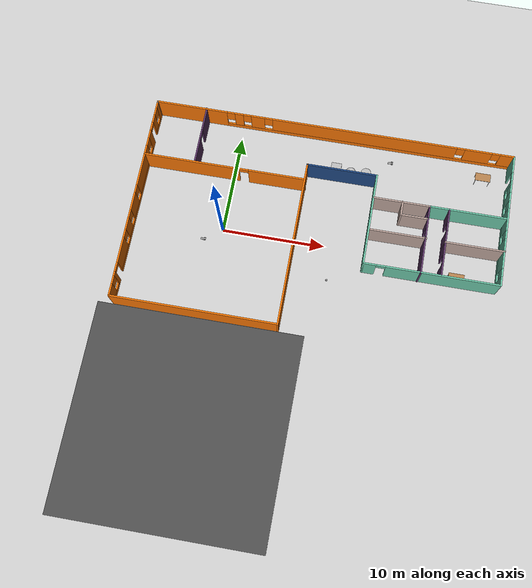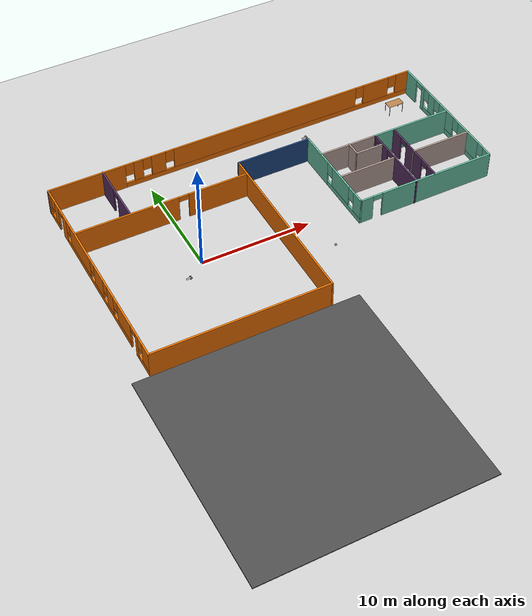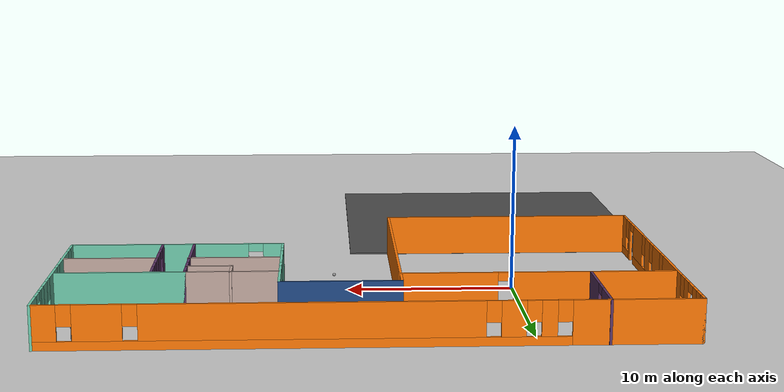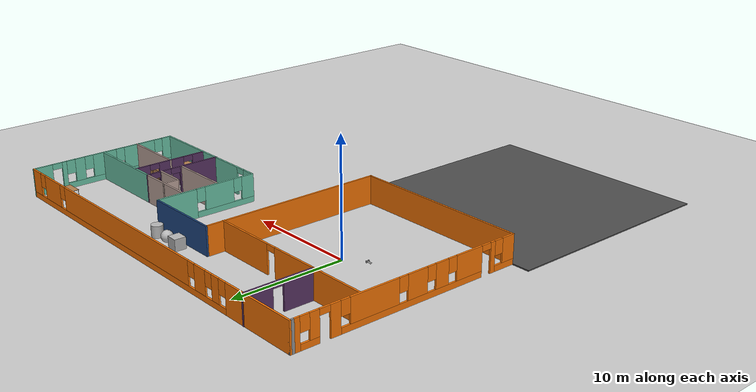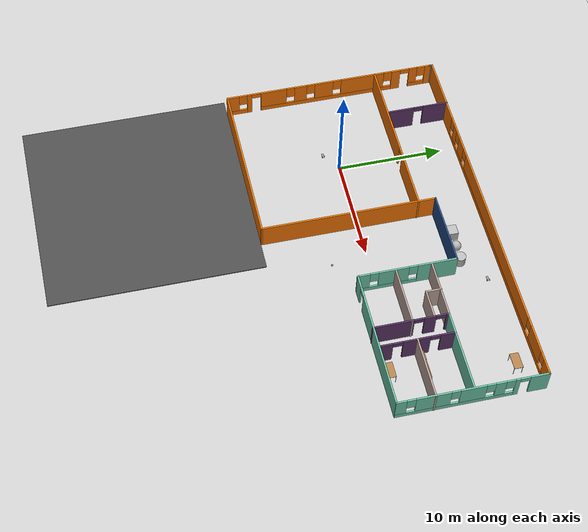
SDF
<sdf version="1.6">
 <world name="default">
  <light name="sun" type="directional">
   <pose>0 0 10 0 -0 0</pose>
   <diffuse>0.8 0.8 0.8 1</diffuse>
   <specular>0.2 0.2 0.2 1</specular>
   <attenuation>
    <range>1000</range>
    <constant>0.9</constant>
    <linear>0.01</linear>
    <quadratic>0.001</quadratic>
   </attenuation>
   <direction>-0.5 0.1 -0.9</direction>
  </light>
  <model name="ground_plane">
   <static>1</static>
   <link name="link">
    <collision name="collision">
     <geometry><plane><normal>0 0 1</normal><size>100 100</size></plane></geometry>
     <surface>
      <contact><collide_bitmask>65535</collide_bitmask></contact>
      <friction><ode><mu>100</mu><mu2>50</mu2></ode></friction>
     </surface>
    </collision>
    <visual name="visual">
     <cast_shadows>0</cast_shadows>
     <geometry><plane><normal>0 0 1</normal><size>100 100</size></plane></geometry>
     <material>
      <script><uri>file://media/materials/scripts/gazebo.material</uri><name>Gazebo/Grey</name></script>
     </material>
    </visual>
   </link>
  </model>
  <gravity>0 0 -9.8</gravity>
  <magnetic_field>6e-06 2.3e-05 -4.2e-05</magnetic_field>
  <atmosphere type="adiabatic"/>
  <physics name="default_physics" default="0" type="ode">
   <max_step_size>0.001</max_step_size>
   <real_time_factor>1</real_time_factor>
   <real_time_update_rate>1000</real_time_update_rate>
  </physics>
  <scene><ambient>0.4 0.4 0.4 1</ambient><background>0.7 0.7 0.7 1</background><shadows>1</shadows></scene>
  <spherical_coordinates>
   <surface_model>EARTH_WGS84</surface_model>
   <latitude_deg>0</latitude_deg>
   <longitude_deg>0</longitude_deg>
   <elevation>0</elevation>
   <heading_deg>0</heading_deg>
  </spherical_coordinates>
  <model name="Thompson">
   <pose>9.07743 1.2048 0 0 -0 0</pose>
   <link name="Wall_15">
    <pose>-0.019631 10.2942 0 0 -0 0</pose>
    <visual name="Wall_15_Visual_0">
     <pose>-14.3246 0 1.25 0 -0 0</pose>
     <geometry><box><size>7.10078 0.15 2.5</size></box></geometry>
     <material>
      <script><uri>file://media/materials/scripts/gazebo.material</uri><name>Gazebo/Grey</name></script>
      <ambient>0.996078 0.47451 0.0196078 1</ambient>
     </material>
     <meta><layer>0</layer></meta>
    </visual>
    <collision name="Wall_15_Collision_0">
     <geometry><box><size>7.10078 0.15 2.5</size></box></geometry>
     <pose>-14.3246 0 1.25 0 -0 0</pose>
    </collision>
    <visual name="Wall_15_Visual_1">
     <pose>3.55039 0 0.25 0 -0 0</pose>
     <geometry><box><size>28.6492 0.15 0.5</size></box></geometry>
     <material>
      <script><uri>file://media/materials/scripts/gazebo.material</uri><name>Gazebo/Grey</name></script>
      <ambient>0.996078 0.47451 0.0196078 1</ambient>
     </material>
     <meta><layer>0</layer></meta>
    </visual>
    <collision name="Wall_15_Collision_1">
     <geometry><box><size>28.6492 0.15 0.5</size></box></geometry>
     <pose>3.55039 0 0.25 0 -0 0</pose>
    </collision>
    <visual name="Wall_15_Visual_2">
     <pose>-9.54752 0 1.5 0 -0 0</pose>
     <geometry><box><size>0.853402 0.15 2</size></box></geometry>
     <material>
      <script><uri>file://media/materials/scripts/gazebo.material</uri><name>Gazebo/Grey</name></script>
      <ambient>0.996078 0.47451 0.0196078 1</ambient>
     </material>
     <meta><layer>0</layer></meta>
    </visual>
    <collision name="Wall_15_Collision_2">
     <geometry><box><size>0.853402 0.15 2</size></box></geometry>
     <pose>-9.54752 0 1.5 0 -0 0</pose>
    </collision>
    <visual name="Wall_15_Visual_3">
     <pose>-7.64786 0 1.5 0 -0 0</pose>
     <geometry><box><size>1.3459 0.15 2</size></box></geometry>
     <material>
      <script><uri>file://media/materials/scripts/gazebo.material</uri><name>Gazebo/Grey</name></script>
      <ambient>0.996078 0.47451 0.0196078 1</ambient>
     </material>
     <meta><layer>0</layer></meta>
    </visual>
    <collision name="Wall_15_Collision_3">
     <geometry><box><size>1.3459 0.15 2</size></box></geometry>
     <pose>-7.64786 0 1.5 0 -0 0</pose>
    </collision>
    <visual name="Wall_15_Visual_4">
     <pose>3.0113 0 1.5 0 -0 0</pose>
     <geometry><box><size>18.3724 0.15 2</size></box></geometry>
     <material>
      <script><uri>file://media/materials/scripts/gazebo.material</uri><name>Gazebo/Grey</name></script>
      <ambient>0.996078 0.47451 0.0196078 1</ambient>
     </material>
     <meta><layer>0</layer></meta>
    </visual>
    <collision name="Wall_15_Collision_4">
     <geometry><box><size>18.3724 0.15 2</size></box></geometry>
     <pose>3.0113 0 1.5 0 -0 0</pose>
    </collision>
    <visual name="Wall_15_Visual_5">
     <pose>14.3213 0 1.5 0 -0 0</pose>
     <geometry><box><size>2.64752 0.15 2</size></box></geometry>
     <material>
      <script><uri>file://media/materials/scripts/gazebo.material</uri><name>Gazebo/Grey</name></script>
      <ambient>0.996078 0.47451 0.0196078 1</ambient>
     </material>
     <meta><layer>0</layer></meta>
    </visual>
    <collision name="Wall_15_Collision_5">
     <geometry><box><size>2.64752 0.15 2</size></box></geometry>
     <pose>14.3213 0 1.5 0 -0 0</pose>
    </collision>
    <visual name="Wall_15_Visual_6">
     <pose>17.16 0 1.5 0 -0 0</pose>
     <geometry><box><size>1.42996 0.15 2</size></box></geometry>
     <material>
      <script><uri>file://media/materials/scripts/gazebo.material</uri><name>Gazebo/Grey</name></script>
      <ambient>0.996078 0.47451 0.0196078 1</ambient>
     </material>
     <meta><layer>0</layer></meta>
    </visual>
    <collision name="Wall_15_Collision_6">
     <geometry><box><size>1.42996 0.15 2</size></box></geometry>
     <pose>17.16 0 1.5 0 -0 0</pose>
    </collision>
    <visual name="Wall_15_Visual_7">
     <pose>-10.3742 0 1.9 0 -0 0</pose>
     <geometry><box><size>0.8 0.15 1.2</size></box></geometry>
     <material>
      <script><uri>file://media/materials/scripts/gazebo.material</uri><name>Gazebo/Grey</name></script>
      <ambient>0.996078 0.47451 0.0196078 1</ambient>
     </material>
     <meta><layer>0</layer></meta>
    </visual>
    <collision name="Wall_15_Collision_7">
     <geometry><box><size>0.8 0.15 1.2</size></box></geometry>
     <pose>-10.3742 0 1.9 0 -0 0</pose>
    </collision>
    <visual name="Wall_15_Visual_8">
     <pose>-8.72081 0 1.9 0 -0 0</pose>
     <geometry><box><size>0.8 0.15 1.2</size></box></geometry>
     <material>
      <script><uri>file://media/materials/scripts/gazebo.material</uri><name>Gazebo/Grey</name></script>
      <ambient>0.996078 0.47451 0.0196078 1</ambient>
     </material>
     <meta><layer>0</layer></meta>
    </visual>
    <collision name="Wall_15_Collision_8">
     <geometry><box><size>0.8 0.15 1.2</size></box></geometry>
     <pose>-8.72081 0 1.9 0 -0 0</pose>
    </collision>
    <visual name="Wall_15_Visual_9">
     <pose>-6.57491 0 1.9 0 -0 0</pose>
     <geometry><box><size>0.8 0.15 1.2</size></box></geometry>
     <material>
      <script><uri>file://media/materials/scripts/gazebo.material</uri><name>Gazebo/Grey</name></script>
      <ambient>0.996078 0.47451 0.0196078 1</ambient>
     </material>
     <meta><layer>0</layer></meta>
    </visual>
    <collision name="Wall_15_Collision_9">
     <geometry><box><size>0.8 0.15 1.2</size></box></geometry>
     <pose>-6.57491 0 1.9 0 -0 0</pose>
    </collision>
    <visual name="Wall_15_Visual_10">
     <pose>12.5975 0 1.9 0 -0 0</pose>
     <geometry><box><size>0.8 0.15 1.2</size></box></geometry>
     <material>
      <script><uri>file://media/materials/scripts/gazebo.material</uri><name>Gazebo/Grey</name></script>
      <ambient>0.996078 0.47451 0.0196078 1</ambient>
     </material>
     <meta><layer>0</layer></meta>
    </visual>
    <collision name="Wall_15_Collision_10">
     <geometry><box><size>0.8 0.15 1.2</size></box></geometry>
     <pose>12.5975 0 1.9 0 -0 0</pose>
    </collision>
    <visual name="Wall_15_Visual_11">
     <pose>16.045 0 1.9 0 -0 0</pose>
     <geometry><box><size>0.8 0.15 1.2</size></box></geometry>
     <material>
      <script><uri>file://media/materials/scripts/gazebo.material</uri><name>Gazebo/Grey</name></script>
      <ambient>0.996078 0.47451 0.0196078 1</ambient>
     </material>
     <meta><layer>0</layer></meta>
    </visual>
    <collision name="Wall_15_Collision_11">
     <geometry><box><size>0.8 0.15 1.2</size></box></geometry>
     <pose>16.045 0 1.9 0 -0 0</pose>
    </collision>
   </link>
   <link name="Wall_16">
    <pose>17.7804 3.61924 0 0 -0 -1.5708</pose>
    <visual name="Wall_16_Visual_0">
     <pose>-5.8837 0 1.25 0 -0 0</pose>
     <geometry><box><size>1.7326 0.15 2.5</size></box></geometry>
     <material>
      <script><uri>file://media/materials/scripts/gazebo.material</uri><name>Gazebo/Grey</name></script>
      <ambient>0.435294 0.796078 0.67451 1</ambient>
     </material>
     <meta><layer>0</layer></meta>
    </visual>
    <collision name="Wall_16_Collision_0">
     <geometry><box><size>1.7326 0.15 2.5</size></box></geometry>
     <pose>-5.8837 0 1.25 0 -0 0</pose>
    </collision>
    <visual name="Wall_16_Visual_1">
     <pose>-3.90918 0 1.25 0 -0 0</pose>
     <geometry><box><size>0.416435 0.15 2.5</size></box></geometry>
     <material>
      <script><uri>file://media/materials/scripts/gazebo.material</uri><name>Gazebo/Grey</name></script>
      <ambient>0.435294 0.796078 0.67451 1</ambient>
     </material>
     <meta><layer>0</layer></meta>
    </visual>
    <collision name="Wall_16_Collision_1">
     <geometry><box><size>0.416435 0.15 2.5</size></box></geometry>
     <pose>-3.90918 0 1.25 0 -0 0</pose>
    </collision>
    <visual name="Wall_16_Visual_2">
     <pose>1.52452 0 0.25 0 -0 0</pose>
     <geometry><box><size>10.451 0.15 0.5</size></box></geometry>
     <material>
      <script><uri>file://media/materials/scripts/gazebo.material</uri><name>Gazebo/Grey</name></script>
      <ambient>0.435294 0.796078 0.67451 1</ambient>
     </material>
     <meta><layer>0</layer></meta>
    </visual>
    <collision name="Wall_16_Collision_2">
     <geometry><box><size>10.451 0.15 0.5</size></box></geometry>
     <pose>1.52452 0 0.25 0 -0 0</pose>
    </collision>
    <visual name="Wall_16_Visual_3">
     <pose>-2.43908 0 1.5 0 -0 0</pose>
     <geometry><box><size>0.92376 0.15 2</size></box></geometry>
     <material>
      <script><uri>file://media/materials/scripts/gazebo.material</uri><name>Gazebo/Grey</name></script>
      <ambient>0.435294 0.796078 0.67451 1</ambient>
     </material>
     <meta><layer>0</layer></meta>
    </visual>
    <collision name="Wall_16_Collision_3">
     <geometry><box><size>0.92376 0.15 2</size></box></geometry>
     <pose>-2.43908 0 1.5 0 -0 0</pose>
    </collision>
    <visual name="Wall_16_Visual_4">
     <pose>-0.033885 0 1.5 0 -0 0</pose>
     <geometry><box><size>2.28664 0.15 2</size></box></geometry>
     <material>
      <script><uri>file://media/materials/scripts/gazebo.material</uri><name>Gazebo/Grey</name></script>
      <ambient>0.435294 0.796078 0.67451 1</ambient>
     </material>
     <meta><layer>0</layer></meta>
    </visual>
    <collision name="Wall_16_Collision_4">
     <geometry><box><size>2.28664 0.15 2</size></box></geometry>
     <pose>-0.033885 0 1.5 0 -0 0</pose>
    </collision>
    <visual name="Wall_16_Visual_5">
     <pose>3.44881 0 1.5 0 -0 0</pose>
     <geometry><box><size>3.07876 0.15 2</size></box></geometry>
     <material>
      <script><uri>file://media/materials/scripts/gazebo.material</uri><name>Gazebo/Grey</name></script>
      <ambient>0.435294 0.796078 0.67451 1</ambient>
     </material>
     <meta><layer>0</layer></meta>
    </visual>
    <collision name="Wall_16_Collision_5">
     <geometry><box><size>3.07876 0.15 2</size></box></geometry>
     <pose>3.44881 0 1.5 0 -0 0</pose>
    </collision>
    <visual name="Wall_16_Visual_6">
     <pose>6.2691 0 1.5 0 -0 0</pose>
     <geometry><box><size>0.96181 0.15 2</size></box></geometry>
     <material>
      <script><uri>file://media/materials/scripts/gazebo.material</uri><name>Gazebo/Grey</name></script>
      <ambient>0.435294 0.796078 0.67451 1</ambient>
     </material>
     <meta><layer>0</layer></meta>
    </visual>
    <collision name="Wall_16_Collision_6">
     <geometry><box><size>0.96181 0.15 2</size></box></geometry>
     <pose>6.2691 0 1.5 0 -0 0</pose>
    </collision>
    <visual name="Wall_16_Visual_7">
     <pose>-3.30097 0 1.9 0 -0 0</pose>
     <geometry><box><size>0.8 0.15 1.2</size></box></geometry>
     <material>
      <script><uri>file://media/materials/scripts/gazebo.material</uri><name>Gazebo/Grey</name></script>
      <ambient>0.435294 0.796078 0.67451 1</ambient>
     </material>
     <meta><layer>0</layer></meta>
    </visual>
    <collision name="Wall_16_Collision_7">
     <geometry><box><size>0.8 0.15 1.2</size></box></geometry>
     <pose>-3.30097 0 1.9 0 -0 0</pose>
    </collision>
    <visual name="Wall_16_Visual_8">
     <pose>-1.5772 0 1.9 0 -0 0</pose>
     <geometry><box><size>0.8 0.15 1.2</size></box></geometry>
     <material>
      <script><uri>file://media/materials/scripts/gazebo.material</uri><name>Gazebo/Grey</name></script>
      <ambient>0.435294 0.796078 0.67451 1</ambient>
     </material>
     <meta><layer>0</layer></meta>
    </visual>
    <collision name="Wall_16_Collision_8">
     <geometry><box><size>0.8 0.15 1.2</size></box></geometry>
     <pose>-1.5772 0 1.9 0 -0 0</pose>
    </collision>
    <visual name="Wall_16_Visual_9">
     <pose>1.50943 0 1.9 0 -0 0</pose>
     <geometry><box><size>0.8 0.15 1.2</size></box></geometry>
     <material>
      <script><uri>file://media/materials/scripts/gazebo.material</uri><name>Gazebo/Grey</name></script>
      <ambient>0.435294 0.796078 0.67451 1</ambient>
     </material>
     <meta><layer>0</layer></meta>
    </visual>
    <collision name="Wall_16_Collision_9">
     <geometry><box><size>0.8 0.15 1.2</size></box></geometry>
     <pose>1.50943 0 1.9 0 -0 0</pose>
    </collision>
    <visual name="Wall_16_Visual_10">
     <pose>5.38819 0 1.9 0 -0 0</pose>
     <geometry><box><size>0.8 0.15 1.2</size></box></geometry>
     <material>
      <script><uri>file://media/materials/scripts/gazebo.material</uri><name>Gazebo/Grey</name></script>
      <ambient>0.435294 0.796078 0.67451 1</ambient>
     </material>
     <meta><layer>0</layer></meta>
    </visual>
    <collision name="Wall_16_Collision_10">
     <geometry><box><size>0.8 0.15 1.2</size></box></geometry>
     <pose>5.38819 0 1.9 0 -0 0</pose>
    </collision>
    <visual name="Wall_16_Visual_11">
     <pose>-4.5674 0 2.25 0 -0 0</pose>
     <geometry><box><size>0.9 0.15 0.5</size></box></geometry>
     <material>
      <script><uri>file://media/materials/scripts/gazebo.material</uri><name>Gazebo/Grey</name></script>
      <ambient>0.435294 0.796078 0.67451 1</ambient>
     </material>
     <meta><layer>0</layer></meta>
    </visual>
    <collision name="Wall_16_Collision_11">
     <geometry><box><size>0.9 0.15 0.5</size></box></geometry>
     <pose>-4.5674 0 2.25 0 -0 0</pose>
    </collision>
   </link>
   <link name="Wall_19">
    <collision name="Wall_19_Collision">
     <geometry><box><size>16.5 0.15 2.5</size></box></geometry>
     <pose>0 0 1.25 0 -0 0</pose>
    </collision>
    <visual name="Wall_19_Visual">
     <pose>0 0 1.25 0 -0 0</pose>
     <geometry><box><size>16.5 0.15 2.5</size></box></geometry>
     <material>
      <script><uri>file://media/materials/scripts/gazebo.material</uri><name>Gazebo/Grey</name></script>
      <ambient>0.996078 0.47451 0.0196078 1</ambient>
     </material>
     <meta><layer>0</layer></meta>
    </visual>
    <pose>-1.97014 -2.15348 0 0 -0 -1.5708</pose>
   </link>
   <link name="Wall_21">
    <pose>4.87986 1.47152 0 0 -0 -1.5708</pose>
    <visual name="Wall_21_Visual_0">
     <pose>-2.79191 0 1.25 0 -0 0</pose>
     <geometry><box><size>3.66617 0.15 2.5</size></box></geometry>
     <material>
      <script><uri>file://media/materials/scripts/gazebo.material</uri><name>Gazebo/Grey</name></script>
      <ambient>0.435294 0.796078 0.67451 1</ambient>
     </material>
     <meta><layer>0</layer></meta>
    </visual>
    <collision name="Wall_21_Collision_0">
     <geometry><box><size>3.66617 0.15 2.5</size></box></geometry>
     <pose>-2.79191 0 1.25 0 -0 0</pose>
    </collision>
    <visual name="Wall_21_Visual_1">
     <pose>1.83309 0 0.25 0 -0 0</pose>
     <geometry><box><size>5.58383 0.15 0.5</size></box></geometry>
     <material>
      <script><uri>file://media/materials/scripts/gazebo.material</uri><name>Gazebo/Grey</name></script>
      <ambient>0.435294 0.796078 0.67451 1</ambient>
     </material>
     <meta><layer>0</layer></meta>
    </visual>
    <collision name="Wall_21_Collision_1">
     <geometry><box><size>5.58383 0.15 0.5</size></box></geometry>
     <pose>1.83309 0 0.25 0 -0 0</pose>
    </collision>
    <visual name="Wall_21_Visual_2">
     <pose>1.23529 0 1.5 0 -0 0</pose>
     <geometry><box><size>2.78823 0.15 2</size></box></geometry>
     <material>
      <script><uri>file://media/materials/scripts/gazebo.material</uri><name>Gazebo/Grey</name></script>
      <ambient>0.435294 0.796078 0.67451 1</ambient>
     </material>
     <meta><layer>0</layer></meta>
    </visual>
    <collision name="Wall_21_Collision_2">
     <geometry><box><size>2.78823 0.15 2</size></box></geometry>
     <pose>1.23529 0 1.5 0 -0 0</pose>
    </collision>
    <visual name="Wall_21_Visual_3">
     <pose>4.0272 0 1.5 0 -0 0</pose>
     <geometry><box><size>1.1956 0.15 2</size></box></geometry>
     <material>
      <script><uri>file://media/materials/scripts/gazebo.material</uri><name>Gazebo/Grey</name></script>
      <ambient>0.435294 0.796078 0.67451 1</ambient>
     </material>
     <meta><layer>0</layer></meta>
    </visual>
    <collision name="Wall_21_Collision_3">
     <geometry><box><size>1.1956 0.15 2</size></box></geometry>
     <pose>4.0272 0 1.5 0 -0 0</pose>
    </collision>
    <visual name="Wall_21_Visual_4">
     <pose>-0.558831 0 1.9 0 -0 0</pose>
     <geometry><box><size>0.8 0.15 1.2</size></box></geometry>
     <material>
      <script><uri>file://media/materials/scripts/gazebo.material</uri><name>Gazebo/Grey</name></script>
      <ambient>0.435294 0.796078 0.67451 1</ambient>
     </material>
     <meta><layer>0</layer></meta>
    </visual>
    <collision name="Wall_21_Collision_4">
     <geometry><box><size>0.8 0.15 1.2</size></box></geometry>
     <pose>-0.558831 0 1.9 0 -0 0</pose>
    </collision>
    <visual name="Wall_21_Visual_5">
     <pose>3.0294 0 1.9 0 -0 0</pose>
     <geometry><box><size>0.8 0.15 1.2</size></box></geometry>
     <material>
      <script><uri>file://media/materials/scripts/gazebo.material</uri><name>Gazebo/Grey</name></script>
      <ambient>0.435294 0.796078 0.67451 1</ambient>
     </material>
     <meta><layer>0</layer></meta>
    </visual>
    <collision name="Wall_21_Collision_5">
     <geometry><box><size>0.8 0.15 1.2</size></box></geometry>
     <pose>3.0294 0 1.9 0 -0 0</pose>
    </collision>
   </link>
   <link name="Wall_23">
    <pose>11.3049 -3.07848 0 0 -0 0</pose>
    <visual name="Wall_23_Visual_0">
     <pose>-5.85955 0 1.25 0 -0 0</pose>
     <geometry><box><size>1.2809 0.15 2.5</size></box></geometry>
     <material>
      <script><uri>file://media/materials/scripts/gazebo.material</uri><name>Gazebo/Grey</name></script>
      <ambient>0.435294 0.796078 0.67451 1</ambient>
     </material>
     <meta><layer>0</layer></meta>
    </visual>
    <collision name="Wall_23_Collision_0">
     <geometry><box><size>1.2809 0.15 2.5</size></box></geometry>
     <pose>-5.85955 0 1.25 0 -0 0</pose>
    </collision>
    <visual name="Wall_23_Visual_1">
     <pose>1.09045 0 1.25 0 -0 0</pose>
     <geometry><box><size>10.8191 0.15 2.5</size></box></geometry>
     <material>
      <script><uri>file://media/materials/scripts/gazebo.material</uri><name>Gazebo/Grey</name></script>
      <ambient>0.435294 0.796078 0.67451 1</ambient>
     </material>
     <meta><layer>0</layer></meta>
    </visual>
    <collision name="Wall_23_Collision_1">
     <geometry><box><size>10.8191 0.15 2.5</size></box></geometry>
     <pose>1.09045 0 1.25 0 -0 0</pose>
    </collision>
    <visual name="Wall_23_Visual_2">
     <pose>-4.7691 0 2.25 0 -0 0</pose>
     <geometry><box><size>0.9 0.15 0.5</size></box></geometry>
     <material>
      <script><uri>file://media/materials/scripts/gazebo.material</uri><name>Gazebo/Grey</name></script>
      <ambient>0.435294 0.796078 0.67451 1</ambient>
     </material>
     <meta><layer>0</layer></meta>
    </visual>
    <collision name="Wall_23_Collision_2">
     <geometry><box><size>0.9 0.15 0.5</size></box></geometry>
     <pose>-4.7691 0 2.25 0 -0 0</pose>
    </collision>
   </link>
   <link name="Wall_25">
    <pose>-9.85667 4.42323 0 0 -0 3.14159</pose>
    <visual name="Wall_25_Visual_0">
     <pose>-5.16838 0 1.25 0 -0 0</pose>
     <geometry><box><size>5.66324 0.15 2.5</size></box></geometry>
     <material>
      <script><uri>file://media/materials/scripts/gazebo.material</uri><name>Gazebo/Grey</name></script>
      <ambient>0.996078 0.47451 0.0196078 1</ambient>
     </material>
     <meta><layer>0</layer></meta>
    </visual>
    <collision name="Wall_25_Collision_0">
     <geometry><box><size>5.66324 0.15 2.5</size></box></geometry>
     <pose>-5.16838 0 1.25 0 -0 0</pose>
    </collision>
    <visual name="Wall_25_Visual_1">
     <pose>3.28162 0 1.25 0 -0 0</pose>
     <geometry><box><size>9.43675 0.15 2.5</size></box></geometry>
     <material>
      <script><uri>file://media/materials/scripts/gazebo.material</uri><name>Gazebo/Grey</name></script>
      <ambient>0.996078 0.47451 0.0196078 1</ambient>
     </material>
     <meta><layer>0</layer></meta>
    </visual>
    <collision name="Wall_25_Collision_1">
     <geometry><box><size>9.43675 0.15 2.5</size></box></geometry>
     <pose>3.28162 0 1.25 0 -0 0</pose>
    </collision>
    <visual name="Wall_25_Visual_2">
     <pose>-1.88675 0 2.25 0 -0 0</pose>
     <geometry><box><size>0.9 0.15 0.5</size></box></geometry>
     <material>
      <script><uri>file://media/materials/scripts/gazebo.material</uri><name>Gazebo/Grey</name></script>
      <ambient>0.996078 0.47451 0.0196078 1</ambient>
     </material>
     <meta><layer>0</layer></meta>
    </visual>
    <collision name="Wall_25_Collision_2">
     <geometry><box><size>0.9 0.15 0.5</size></box></geometry>
     <pose>-1.88675 0 2.25 0 -0 0</pose>
    </collision>
   </link>
   <link name="Wall_27">
    <pose>-12.8378 7.40348 0 0 -0 -1.5708</pose>
    <visual name="Wall_27_Visual_0">
     <pose>-1.76439 0 1.25 0 -0 0</pose>
     <geometry><box><size>2.47122 0.15 2.5</size></box></geometry>
     <material>
      <script><uri>file://media/materials/scripts/gazebo.material</uri><name>Gazebo/Grey</name></script>
      <ambient>0.360784 0.207843 0.4 1</ambient>
     </material>
     <meta><layer>0</layer></meta>
    </visual>
    <collision name="Wall_27_Collision_0">
     <geometry><box><size>2.47122 0.15 2.5</size></box></geometry>
     <pose>-1.76439 0 1.25 0 -0 0</pose>
    </collision>
    <visual name="Wall_27_Visual_1">
     <pose>1.68561 0 1.25 0 -0 0</pose>
     <geometry><box><size>2.62878 0.15 2.5</size></box></geometry>
     <material>
      <script><uri>file://media/materials/scripts/gazebo.material</uri><name>Gazebo/Grey</name></script>
      <ambient>0.360784 0.207843 0.4 1</ambient>
     </material>
     <meta><layer>0</layer></meta>
    </visual>
    <collision name="Wall_27_Collision_1">
     <geometry><box><size>2.62878 0.15 2.5</size></box></geometry>
     <pose>1.68561 0 1.25 0 -0 0</pose>
    </collision>
    <visual name="Wall_27_Visual_2">
     <pose>-0.078778 0 2.25 0 -0 0</pose>
     <geometry><box><size>0.9 0.15 0.5</size></box></geometry>
     <material>
      <script><uri>file://media/materials/scripts/gazebo.material</uri><name>Gazebo/Grey</name></script>
      <ambient>0.360784 0.207843 0.4 1</ambient>
     </material>
     <meta><layer>0</layer></meta>
    </visual>
    <collision name="Wall_27_Collision_2">
     <geometry><box><size>0.9 0.15 0.5</size></box></geometry>
     <pose>-0.078778 0 2.25 0 -0 0</pose>
    </collision>
   </link>
   <link name="Wall_3">
    <pose>-17.8196 -0.130763 0 0 -0 -1.5708</pose>
    <visual name="Wall_3_Visual_0">
     <pose>-9.95861 0 1.25 0 -0 0</pose>
     <geometry><box><size>0.582773 0.15 2.5</size></box></geometry>
     <material>
      <script><uri>file://media/materials/scripts/gazebo.material</uri><name>Gazebo/Grey</name></script>
      <ambient>0.996078 0.47451 0.0196078 1</ambient>
     </material>
     <meta><layer>0</layer></meta>
    </visual>
    <collision name="Wall_3_Collision_0">
     <geometry><box><size>0.582773 0.15 2.5</size></box></geometry>
     <pose>-9.95861 0 1.25 0 -0 0</pose>
    </collision>
    <visual name="Wall_3_Visual_1">
     <pose>-6.72654 0 1.25 0 -0 0</pose>
     <geometry><box><size>0.872952 0.15 2.5</size></box></geometry>
     <material>
      <script><uri>file://media/materials/scripts/gazebo.material</uri><name>Gazebo/Grey</name></script>
      <ambient>0.996078 0.47451 0.0196078 1</ambient>
     </material>
     <meta><layer>0</layer></meta>
    </visual>
    <collision name="Wall_3_Collision_1">
     <geometry><box><size>0.872952 0.15 2.5</size></box></geometry>
     <pose>-6.72654 0 1.25 0 -0 0</pose>
    </collision>
    <visual name="Wall_3_Visual_2">
     <pose>8.01044 0 1.25 0 -0 0</pose>
     <geometry><box><size>0.448286 0.15 2.5</size></box></geometry>
     <material>
      <script><uri>file://media/materials/scripts/gazebo.material</uri><name>Gazebo/Grey</name></script>
      <ambient>0.996078 0.47451 0.0196078 1</ambient>
     </material>
     <meta><layer>0</layer></meta>
    </visual>
    <collision name="Wall_3_Collision_2">
     <geometry><box><size>0.448286 0.15 2.5</size></box></geometry>
     <pose>8.01044 0 1.25 0 -0 0</pose>
    </collision>
    <visual name="Wall_3_Visual_3">
     <pose>-8.86512 0 0.25 0 -0 0</pose>
     <geometry><box><size>1.60421 0.15 0.5</size></box></geometry>
     <material>
      <script><uri>file://media/materials/scripts/gazebo.material</uri><name>Gazebo/Grey</name></script>
      <ambient>0.996078 0.47451 0.0196078 1</ambient>
     </material>
     <meta><layer>0</layer></meta>
    </visual>
    <collision name="Wall_3_Collision_3">
     <geometry><box><size>1.60421 0.15 0.5</size></box></geometry>
     <pose>-8.86512 0 0.25 0 -0 0</pose>
    </collision>
    <visual name="Wall_3_Visual_4">
     <pose>0.298114 0 0.25 0 -0 0</pose>
     <geometry><box><size>13.1764 0.15 0.5</size></box></geometry>
     <material>
      <script><uri>file://media/materials/scripts/gazebo.material</uri><name>Gazebo/Grey</name></script>
      <ambient>0.996078 0.47451 0.0196078 1</ambient>
     </material>
     <meta><layer>0</layer></meta>
    </visual>
    <collision name="Wall_3_Collision_4">
     <geometry><box><size>13.1764 0.15 0.5</size></box></geometry>
     <pose>0.298114 0 0.25 0 -0 0</pose>
    </collision>
    <visual name="Wall_3_Visual_5">
     <pose>9.24229 0 0.25 0 -0 0</pose>
     <geometry><box><size>2.01542 0.15 0.5</size></box></geometry>
     <material>
      <script><uri>file://media/materials/scripts/gazebo.material</uri><name>Gazebo/Grey</name></script>
      <ambient>0.996078 0.47451 0.0196078 1</ambient>
     </material>
     <meta><layer>0</layer></meta>
    </visual>
    <collision name="Wall_3_Collision_5">
     <geometry><box><size>2.01542 0.15 0.5</size></box></geometry>
     <pose>9.24229 0 0.25 0 -0 0</pose>
    </collision>
    <visual name="Wall_3_Visual_6">
     <pose>-8.46512 0 1.5 0 -0 0</pose>
     <geometry><box><size>0.804209 0.15 2</size></box></geometry>
     <material>
      <script><uri>file://media/materials/scripts/gazebo.material</uri><name>Gazebo/Grey</name></script>
      <ambient>0.996078 0.47451 0.0196078 1</ambient>
     </material>
     <meta><layer>0</layer></meta>
    </visual>
    <collision name="Wall_3_Collision_6">
     <geometry><box><size>0.804209 0.15 2</size></box></geometry>
     <pose>-8.46512 0 1.5 0 -0 0</pose>
    </collision>
    <visual name="Wall_3_Visual_7">
     <pose>-8.46512 0 1.5 0 -0 0</pose>
     <geometry><box><size>0.804209 0.15 2</size></box></geometry>
     <material>
      <script><uri>file://media/materials/scripts/gazebo.material</uri><name>Gazebo/Grey</name></script>
      <ambient>0.996078 0.47451 0.0196078 1</ambient>
     </material>
     <meta><layer>0</layer></meta>
    </visual>
    <collision name="Wall_3_Collision_7">
     <geometry><box><size>0.804209 0.15 2</size></box></geometry>
     <pose>-8.46512 0 1.5 0 -0 0</pose>
    </collision>
    <visual name="Wall_3_Visual_8">
     <pose>-3.32202 0 1.5 0 -0 0</pose>
     <geometry><box><size>4.3361 0.15 2</size></box></geometry>
     <material>
      <script><uri>file://media/materials/scripts/gazebo.material</uri><name>Gazebo/Grey</name></script>
      <ambient>0.996078 0.47451 0.0196078 1</ambient>
     </material>
     <meta><layer>0</layer></meta>
    </visual>
    <collision name="Wall_3_Collision_8">
     <geometry><box><size>4.3361 0.15 2</size></box></geometry>
     <pose>-3.32202 0 1.5 0 -0 0</pose>
    </collision>
    <visual name="Wall_3_Visual_9">
     <pose>0.565237 0 1.5 0 -0 0</pose>
     <geometry><box><size>1.83841 0.15 2</size></box></geometry>
     <material>
      <script><uri>file://media/materials/scripts/gazebo.material</uri><name>Gazebo/Grey</name></script>
      <ambient>0.996078 0.47451 0.0196078 1</ambient>
     </material>
     <meta><layer>0</layer></meta>
    </visual>
    <collision name="Wall_3_Collision_9">
     <geometry><box><size>1.83841 0.15 2</size></box></geometry>
     <pose>0.565237 0 1.5 0 -0 0</pose>
    </collision>
    <visual name="Wall_3_Visual_10">
     <pose>2.90462 0 1.5 0 -0 0</pose>
     <geometry><box><size>1.24037 0.15 2</size></box></geometry>
     <material>
      <script><uri>file://media/materials/scripts/gazebo.material</uri><name>Gazebo/Grey</name></script>
      <ambient>0.996078 0.47451 0.0196078 1</ambient>
     </material>
     <meta><layer>0</layer></meta>
    </visual>
    <collision name="Wall_3_Collision_10">
     <geometry><box><size>1.24037 0.15 2</size></box></geometry>
     <pose>2.90462 0 1.5 0 -0 0</pose>
    </collision>
    <visual name="Wall_3_Visual_11">
     <pose>5.60555 0 1.5 0 -0 0</pose>
     <geometry><box><size>2.56148 0.15 2</size></box></geometry>
     <material>
      <script><uri>file://media/materials/scripts/gazebo.material</uri><name>Gazebo/Grey</name></script>
      <ambient>0.996078 0.47451 0.0196078 1</ambient>
     </material>
     <meta><layer>0</layer></meta>
    </visual>
    <collision name="Wall_3_Collision_11">
     <geometry><box><size>2.56148 0.15 2</size></box></geometry>
     <pose>5.60555 0 1.5 0 -0 0</pose>
    </collision>
    <visual name="Wall_3_Visual_12">
     <pose>5.60555 0 1.5 0 -0 0</pose>
     <geometry><box><size>2.56148 0.15 2</size></box></geometry>
     <material>
      <script><uri>file://media/materials/scripts/gazebo.material</uri><name>Gazebo/Grey</name></script>
      <ambient>0.996078 0.47451 0.0196078 1</ambient>
     </material>
     <meta><layer>0</layer></meta>
    </visual>
    <collision name="Wall_3_Collision_12">
     <geometry><box><size>2.56148 0.15 2</size></box></geometry>
     <pose>5.60555 0 1.5 0 -0 0</pose>
    </collision>
    <visual name="Wall_3_Visual_13">
     <pose>9.64229 0 1.5 0 -0 0</pose>
     <geometry><box><size>1.21542 0.15 2</size></box></geometry>
     <material>
      <script><uri>file://media/materials/scripts/gazebo.material</uri><name>Gazebo/Grey</name></script>
      <ambient>0.996078 0.47451 0.0196078 1</ambient>
     </material>
     <meta><layer>0</layer></meta>
    </visual>
    <collision name="Wall_3_Collision_13">
     <geometry><box><size>1.21542 0.15 2</size></box></geometry>
     <pose>9.64229 0 1.5 0 -0 0</pose>
    </collision>
    <visual name="Wall_3_Visual_14">
     <pose>-9.26723 0 1.9 0 -0 0</pose>
     <geometry><box><size>0.8 0.15 1.2</size></box></geometry>
     <material>
      <script><uri>file://media/materials/scripts/gazebo.material</uri><name>Gazebo/Grey</name></script>
      <ambient>0.996078 0.47451 0.0196078 1</ambient>
     </material>
     <meta><layer>0</layer></meta>
    </visual>
    <collision name="Wall_3_Collision_14">
     <geometry><box><size>0.8 0.15 1.2</size></box></geometry>
     <pose>-9.26723 0 1.9 0 -0 0</pose>
    </collision>
    <visual name="Wall_3_Visual_15">
     <pose>-5.89006 0 1.9 0 -0 0</pose>
     <geometry><box><size>0.8 0.15 1.2</size></box></geometry>
     <material>
      <script><uri>file://media/materials/scripts/gazebo.material</uri><name>Gazebo/Grey</name></script>
      <ambient>0.996078 0.47451 0.0196078 1</ambient>
     </material>
     <meta><layer>0</layer></meta>
    </visual>
    <collision name="Wall_3_Collision_15">
     <geometry><box><size>0.8 0.15 1.2</size></box></geometry>
     <pose>-5.89006 0 1.9 0 -0 0</pose>
    </collision>
    <visual name="Wall_3_Visual_16">
     <pose>8.63458 0 1.9 0 -0 0</pose>
     <geometry><box><size>0.8 0.15 1.2</size></box></geometry>
     <material>
      <script><uri>file://media/materials/scripts/gazebo.material</uri><name>Gazebo/Grey</name></script>
      <ambient>0.996078 0.47451 0.0196078 1</ambient>
     </material>
     <meta><layer>0</layer></meta>
    </visual>
    <collision name="Wall_3_Collision_16">
     <geometry><box><size>0.8 0.15 1.2</size></box></geometry>
     <pose>8.63458 0 1.9 0 -0 0</pose>
    </collision>
    <visual name="Wall_3_Visual_17">
     <pose>-0.753966 0 1.9 0 -0 0</pose>
     <geometry><box><size>0.8 0.15 1.2</size></box></geometry>
     <material>
      <script><uri>file://media/materials/scripts/gazebo.material</uri><name>Gazebo/Grey</name></script>
      <ambient>0.996078 0.47451 0.0196078 1</ambient>
     </material>
     <meta><layer>0</layer></meta>
    </visual>
    <collision name="Wall_3_Collision_17">
     <geometry><box><size>0.8 0.15 1.2</size></box></geometry>
     <pose>-0.753966 0 1.9 0 -0 0</pose>
    </collision>
    <visual name="Wall_3_Visual_18">
     <pose>1.88444 0 1.9 0 -0 0</pose>
     <geometry><box><size>0.8 0.15 1.2</size></box></geometry>
     <material>
      <script><uri>file://media/materials/scripts/gazebo.material</uri><name>Gazebo/Grey</name></script>
      <ambient>0.996078 0.47451 0.0196078 1</ambient>
     </material>
     <meta><layer>0</layer></meta>
    </visual>
    <collision name="Wall_3_Collision_18">
     <geometry><box><size>0.8 0.15 1.2</size></box></geometry>
     <pose>1.88444 0 1.9 0 -0 0</pose>
    </collision>
    <visual name="Wall_3_Visual_19">
     <pose>3.92481 0 1.9 0 -0 0</pose>
     <geometry><box><size>0.8 0.15 1.2</size></box></geometry>
     <material>
      <script><uri>file://media/materials/scripts/gazebo.material</uri><name>Gazebo/Grey</name></script>
      <ambient>0.996078 0.47451 0.0196078 1</ambient>
     </material>
     <meta><layer>0</layer></meta>
    </visual>
    <collision name="Wall_3_Collision_19">
     <geometry><box><size>0.8 0.15 1.2</size></box></geometry>
     <pose>3.92481 0 1.9 0 -0 0</pose>
    </collision>
    <visual name="Wall_3_Visual_20">
     <pose>-7.61302 0 2.25 0 -0 0</pose>
     <geometry><box><size>0.9 0.15 0.5</size></box></geometry>
     <material>
      <script><uri>file://media/materials/scripts/gazebo.material</uri><name>Gazebo/Grey</name></script>
      <ambient>0.996078 0.47451 0.0196078 1</ambient>
     </material>
     <meta><layer>0</layer></meta>
    </visual>
    <collision name="Wall_3_Collision_20">
     <geometry><box><size>0.9 0.15 0.5</size></box></geometry>
     <pose>-7.61302 0 2.25 0 -0 0</pose>
    </collision>
    <visual name="Wall_3_Visual_21">
     <pose>-7.61302 0 2.25 0 -0 0</pose>
     <geometry><box><size>0.9 0.15 0.5</size></box></geometry>
     <material>
      <script><uri>file://media/materials/scripts/gazebo.material</uri><name>Gazebo/Grey</name></script>
      <ambient>0.996078 0.47451 0.0196078 1</ambient>
     </material>
     <meta><layer>0</layer></meta>
    </visual>
    <collision name="Wall_3_Collision_21">
     <geometry><box><size>0.9 0.15 0.5</size></box></geometry>
     <pose>-7.61302 0 2.25 0 -0 0</pose>
    </collision>
    <visual name="Wall_3_Visual_22">
     <pose>7.33629 0 2.25 0 -0 0</pose>
     <geometry><box><size>0.9 0.15 0.5</size></box></geometry>
     <material>
      <script><uri>file://media/materials/scripts/gazebo.material</uri><name>Gazebo/Grey</name></script>
      <ambient>0.996078 0.47451 0.0196078 1</ambient>
     </material>
     <meta><layer>0</layer></meta>
    </visual>
    <collision name="Wall_3_Collision_22">
     <geometry><box><size>0.9 0.15 0.5</size></box></geometry>
     <pose>7.33629 0 2.25 0 -0 0</pose>
    </collision>
    <visual name="Wall_3_Visual_23">
     <pose>7.33629 0 2.25 0 -0 0</pose>
     <geometry><box><size>0.9 0.15 0.5</size></box></geometry>
     <material>
      <script><uri>file://media/materials/scripts/gazebo.material</uri><name>Gazebo/Grey</name></script>
      <ambient>0.996078 0.47451 0.0196078 1</ambient>
     </material>
     <meta><layer>0</layer></meta>
    </visual>
    <collision name="Wall_3_Collision_23">
     <geometry><box><size>0.9 0.15 0.5</size></box></geometry>
     <pose>7.33629 0 2.25 0 -0 0</pose>
    </collision>
   </link>
   <link name="Wall_30">
    <pose>10.3078 0.286514 0 0 -0 -1.5708</pose>
    <visual name="Wall_30_Visual_0">
     <pose>-3.31288 0 1.25 0 -0 0</pose>
     <geometry><box><size>0.334019 0.15 2.5</size></box></geometry>
     <material>
      <script><uri>file://media/materials/scripts/gazebo.material</uri><name>Gazebo/Grey</name></script>
      <ambient>0.360784 0.207843 0.4 1</ambient>
     </material>
     <meta><layer>0</layer></meta>
    </visual>
    <collision name="Wall_30_Collision_0">
     <geometry><box><size>0.334019 0.15 2.5</size></box></geometry>
     <pose>-3.31288 0 1.25 0 -0 0</pose>
    </collision>
    <visual name="Wall_30_Visual_1">
     <pose>-1.71609 0 1.25 0 -0 0</pose>
     <geometry><box><size>1.05955 0.15 2.5</size></box></geometry>
     <material>
      <script><uri>file://media/materials/scripts/gazebo.material</uri><name>Gazebo/Grey</name></script>
      <ambient>0.360784 0.207843 0.4 1</ambient>
     </material>
     <meta><layer>0</layer></meta>
    </visual>
    <collision name="Wall_30_Collision_1">
     <geometry><box><size>1.05955 0.15 2.5</size></box></geometry>
     <pose>-1.71609 0 1.25 0 -0 0</pose>
    </collision>
    <visual name="Wall_30_Visual_2">
     <pose>1.59679 0 1.25 0 -0 0</pose>
     <geometry><box><size>3.7662 0.15 2.5</size></box></geometry>
     <material>
      <script><uri>file://media/materials/scripts/gazebo.material</uri><name>Gazebo/Grey</name></script>
      <ambient>0.360784 0.207843 0.4 1</ambient>
     </material>
     <meta><layer>0</layer></meta>
    </visual>
    <collision name="Wall_30_Collision_2">
     <geometry><box><size>3.7662 0.15 2.5</size></box></geometry>
     <pose>1.59679 0 1.25 0 -0 0</pose>
    </collision>
    <visual name="Wall_30_Visual_3">
     <pose>-2.69587 0 2.25 0 -0 0</pose>
     <geometry><box><size>0.9 0.15 0.5</size></box></geometry>
     <material>
      <script><uri>file://media/materials/scripts/gazebo.material</uri><name>Gazebo/Grey</name></script>
      <ambient>0.360784 0.207843 0.4 1</ambient>
     </material>
     <meta><layer>0</layer></meta>
    </visual>
    <collision name="Wall_30_Collision_3">
     <geometry><box><size>0.9 0.15 0.5</size></box></geometry>
     <pose>-2.69587 0 2.25 0 -0 0</pose>
    </collision>
    <visual name="Wall_30_Visual_4">
     <pose>-0.736313 0 2.25 0 -0 0</pose>
     <geometry><box><size>0.9 0.15 0.5</size></box></geometry>
     <material>
      <script><uri>file://media/materials/scripts/gazebo.material</uri><name>Gazebo/Grey</name></script>
      <ambient>0.360784 0.207843 0.4 1</ambient>
     </material>
     <meta><layer>0</layer></meta>
    </visual>
    <collision name="Wall_30_Collision_4">
     <geometry><box><size>0.9 0.15 0.5</size></box></geometry>
     <pose>-0.736313 0 2.25 0 -0 0</pose>
    </collision>
   </link>
   <link name="Wall_36">
    <collision name="Wall_36_Collision">
     <geometry><box><size>5.75 0.15 2.5</size></box></geometry>
     <pose>0 0 1.25 0 -0 0</pose>
    </collision>
    <visual name="Wall_36_Visual">
     <pose>0 0 1.25 0 -0 0</pose>
     <geometry><box><size>5.75 0.15 2.5</size></box></geometry>
     <material>
      <script><uri>file://media/materials/scripts/gazebo.material</uri><name>Gazebo/Grey</name></script>
      <ambient>0.760784 0.662745 0.627451 1</ambient>
     </material>
     <meta><layer>0</layer></meta>
    </visual>
    <pose>15.0196 0.326802 0 0 -0 0</pose>
   </link>
   <link name="Wall_38">
    <collision name="Wall_38_Collision">
     <geometry><box><size>5.5 0.15 2.5</size></box></geometry>
     <pose>0 0 1.25 0 -0 0</pose>
    </collision>
    <visual name="Wall_38_Visual">
     <pose>0 0 1.25 0 -0 0</pose>
     <geometry><box><size>5.5 0.15 2.5</size></box></geometry>
     <material>
      <script><uri>file://media/materials/scripts/gazebo.material</uri><name>Gazebo/Grey</name></script>
      <ambient>0.760784 0.662745 0.627451 1</ambient>
     </material>
     <meta><layer>0</layer></meta>
    </visual>
    <pose>7.68262 0.380002 0 0 -0 3.14159</pose>
   </link>
   <link name="Wall_4">
    <collision name="Wall_4_Collision">
     <geometry><box><size>16 0.15 2.5</size></box></geometry>
     <pose>0 0 1.25 0 -0 0</pose>
    </collision>
    <visual name="Wall_4_Visual">
     <pose>0 0 1.25 0 -0 0</pose>
     <geometry><box><size>16 0.15 2.5</size></box></geometry>
     <material>
      <script><uri>file://media/materials/scripts/gazebo.material</uri><name>Gazebo/Grey</name></script>
      <ambient>0.996078 0.47451 0.0196078 1</ambient>
     </material>
     <meta><layer>0</layer></meta>
    </visual>
    <pose>-9.89463 -10.3058 0 0 -0 0</pose>
   </link>
   <link name="Wall_47">
    <collision name="Wall_47_Collision">
     <geometry><box><size>2.75 0.15 2.5</size></box></geometry>
     <pose>0 0 1.25 0 -0 0</pose>
    </collision>
    <visual name="Wall_47_Visual">
     <pose>0 0 1.25 0 -0 0</pose>
     <geometry><box><size>2.75 0.15 2.5</size></box></geometry>
     <material>
      <script><uri>file://media/materials/scripts/gazebo.material</uri><name>Gazebo/Grey</name></script>
      <ambient>0.760784 0.662745 0.627451 1</ambient>
     </material>
     <meta><layer>0</layer></meta>
    </visual>
    <pose>8.9976 2.37502 0 0 -0 0</pose>
   </link>
   <link name="Wall_51">
    <collision name="Wall_51_Collision">
     <geometry><box><size>5.5 0.15 2.5</size></box></geometry>
     <pose>0 0 1.25 0 -0 0</pose>
    </collision>
    <visual name="Wall_51_Visual">
     <pose>0 0 1.25 0 -0 0</pose>
     <geometry><box><size>5.5 0.15 2.5</size></box></geometry>
     <material>
      <script><uri>file://media/materials/scripts/gazebo.material</uri><name>Gazebo/Grey</name></script>
      <ambient>0.760784 0.662745 0.627451 1</ambient>
     </material>
     <meta><layer>0</layer></meta>
    </visual>
    <pose>7.63278 3.6914 0 0 -0 3.14159</pose>
   </link>
   <link name="Wall_55">
    <pose>12.2196 -1.3482 0 0 -0 -1.5708</pose>
    <visual name="Wall_55_Visual_0">
     <pose>-1.06552 0 1.25 0 -0 0</pose>
     <geometry><box><size>1.36897 0.15 2.5</size></box></geometry>
     <material>
      <script><uri>file://media/materials/scripts/gazebo.material</uri><name>Gazebo/Grey</name></script>
      <ambient>0.360784 0.207843 0.4 1</ambient>
     </material>
     <meta><layer>0</layer></meta>
    </visual>
    <collision name="Wall_55_Collision_0">
     <geometry><box><size>1.36897 0.15 2.5</size></box></geometry>
     <pose>-1.06552 0 1.25 0 -0 0</pose>
    </collision>
    <visual name="Wall_55_Visual_1">
     <pose>1.13448 0 1.25 0 -0 0</pose>
     <geometry><box><size>1.23103 0.15 2.5</size></box></geometry>
     <material>
      <script><uri>file://media/materials/scripts/gazebo.material</uri><name>Gazebo/Grey</name></script>
      <ambient>0.360784 0.207843 0.4 1</ambient>
     </material>
     <meta><layer>0</layer></meta>
    </visual>
    <collision name="Wall_55_Collision_1">
     <geometry><box><size>1.23103 0.15 2.5</size></box></geometry>
     <pose>1.13448 0 1.25 0 -0 0</pose>
    </collision>
    <visual name="Wall_55_Visual_2">
     <pose>0.068967 0 2.25 0 -0 0</pose>
     <geometry><box><size>0.9 0.15 0.5</size></box></geometry>
     <material>
      <script><uri>file://media/materials/scripts/gazebo.material</uri><name>Gazebo/Grey</name></script>
      <ambient>0.360784 0.207843 0.4 1</ambient>
     </material>
     <meta><layer>0</layer></meta>
    </visual>
    <collision name="Wall_55_Collision_2">
     <geometry><box><size>0.9 0.15 0.5</size></box></geometry>
     <pose>0.068967 0 2.25 0 -0 0</pose>
    </collision>
   </link>
   <link name="Wall_57">
    <collision name="Wall_57_Collision">
     <geometry><box><size>7.5 0.15 2.5</size></box></geometry>
     <pose>0 0 1.25 0 -0 0</pose>
    </collision>
    <visual name="Wall_57_Visual">
     <pose>0 0 1.25 0 -0 0</pose>
     <geometry><box><size>7.5 0.15 2.5</size></box></geometry>
     <material>
      <script><uri>file://media/materials/scripts/gazebo.material</uri><name>Gazebo/Grey</name></script>
      <ambient>0.435294 0.796078 0.67451 1</ambient>
     </material>
     <meta><layer>0</layer></meta>
    </visual>
    <pose>13.9828 3.6914 0 0 -0 0</pose>
   </link>
   <link name="Wall_59">
    <pose>12.2196 2.0018 0 0 -0 1.5708</pose>
    <visual name="Wall_59_Visual_0">
     <pose>-1.13849 0 1.25 0 -0 0</pose>
     <geometry><box><size>1.22302 0.15 2.5</size></box></geometry>
     <material>
      <script><uri>file://media/materials/scripts/gazebo.material</uri><name>Gazebo/Grey</name></script>
      <ambient>0.360784 0.207843 0.4 1</ambient>
     </material>
     <meta><layer>0</layer></meta>
    </visual>
    <collision name="Wall_59_Collision_0">
     <geometry><box><size>1.22302 0.15 2.5</size></box></geometry>
     <pose>-1.13849 0 1.25 0 -0 0</pose>
    </collision>
    <visual name="Wall_59_Visual_1">
     <pose>1.06151 0 1.25 0 -0 0</pose>
     <geometry><box><size>1.37698 0.15 2.5</size></box></geometry>
     <material>
      <script><uri>file://media/materials/scripts/gazebo.material</uri><name>Gazebo/Grey</name></script>
      <ambient>0.360784 0.207843 0.4 1</ambient>
     </material>
     <meta><layer>0</layer></meta>
    </visual>
    <collision name="Wall_59_Collision_1">
     <geometry><box><size>1.37698 0.15 2.5</size></box></geometry>
     <pose>1.06151 0 1.25 0 -0 0</pose>
    </collision>
    <visual name="Wall_59_Visual_2">
     <pose>-0.076984 0 2.25 0 -0 0</pose>
     <geometry><box><size>0.9 0.15 0.5</size></box></geometry>
     <material>
      <script><uri>file://media/materials/scripts/gazebo.material</uri><name>Gazebo/Grey</name></script>
      <ambient>0.360784 0.207843 0.4 1</ambient>
     </material>
     <meta><layer>0</layer></meta>
    </visual>
    <collision name="Wall_59_Collision_2">
     <geometry><box><size>0.9 0.15 0.5</size></box></geometry>
     <pose>-0.076984 0 2.25 0 -0 0</pose>
    </collision>
   </link>
   <link name="Wall_65">
    <collision name="Wall_65_Collision">
     <geometry><box><size>1.5 0.15 2.5</size></box></geometry>
     <pose>0 0 1.25 0 -0 0</pose>
    </collision>
    <visual name="Wall_65_Visual">
     <pose>0 0 1.25 0 -0 0</pose>
     <geometry><box><size>1.5 0.15 2.5</size></box></geometry>
     <material>
      <script><uri>file://media/materials/scripts/gazebo.material</uri><name>Gazebo/Grey</name></script>
      <ambient>0.760784 0.662745 0.627451 1</ambient>
     </material>
     <meta><layer>0</layer></meta>
    </visual>
    <pose>7.6976 3.05002 0 0 -0 1.5708</pose>
   </link>
   <link name="Wall_7">
    <collision name="Wall_7_Collision">
     <geometry><box><size>0.4 0.15 2.5</size></box></geometry>
     <pose>0 0 1.25 0 -0 0</pose>
    </collision>
    <visual name="Wall_7_Visual">
     <pose>0 0 1.25 0 -0 0</pose>
     <geometry><box><size>0.4 0.15 2.5</size></box></geometry>
     <material>
      <script><uri>file://media/materials/scripts/gazebo.material</uri><name>Gazebo/Grey</name></script>
      <ambient>1 1 1 1</ambient>
     </material>
     <meta><layer>0</layer></meta>
    </visual>
    <pose>-17.8196 10.1692 0 0 -0 -1.5708</pose>
   </link>
   <link name="Wall_9">
    <collision name="Wall_9_Collision">
     <geometry><box><size>7 0.15 2.5</size></box></geometry>
     <pose>0 0 1.25 0 -0 0</pose>
    </collision>
    <visual name="Wall_9_Visual">
     <pose>0 0 1.25 0 -0 0</pose>
     <geometry><box><size>7 0.15 2.5</size></box></geometry>
     <material>
      <script><uri>file://media/materials/scripts/gazebo.material</uri><name>Gazebo/Grey</name></script>
      <ambient>0.12549 0.290196 0.529412 1</ambient>
     </material>
     <meta><layer>0</layer></meta>
    </visual>
    <pose>1.45486 6.02152 0 0 -0 0</pose>
   </link>
   <static>1</static>
  </model>
  <model name="bookshelf">
   <static>1</static>
   <link name="link">
    <inertial><mass>1</mass></inertial>
    <collision name="back">
     <pose>0 0.005 0.6 0 -0 0</pose>
     <geometry><box><size>0.9 0.01 1.2</size></box></geometry>
    </collision>
    <visual name="visual1">
     <pose>0 0.005 0.6 0 -0 0</pose>
     <geometry><box><size>0.9 0.01 1.2</size></box></geometry>
     <material>
      <script><uri>file://media/materials/scripts/gazebo.material</uri><name>Gazebo/Wood</name></script>
     </material>
    </visual>
    <collision name="left_side">
     <pose>0.45 -0.195 0.6 0 -0 0</pose>
     <geometry><box><size>0.02 0.4 1.2</size></box></geometry>
    </collision>
    <visual name="visual2">
     <pose>0.45 -0.195 0.6 0 -0 0</pose>
     <geometry><box><size>0.02 0.4 1.2</size></box></geometry>
     <material>
      <script><uri>file://media/materials/scripts/gazebo.material</uri><name>Gazebo/Wood</name></script>
     </material>
    </visual>
    <collision name="right_side">
     <pose>-0.45 -0.195 0.6 0 -0 0</pose>
     <geometry><box><size>0.02 0.4 1.2</size></box></geometry>
    </collision>
    <visual name="visual3">
     <pose>-0.45 -0.195 0.6 0 -0 0</pose>
     <geometry><box><size>0.02 0.4 1.2</size></box></geometry>
     <material>
      <script><uri>file://media/materials/scripts/gazebo.material</uri><name>Gazebo/Wood</name></script>
     </material>
    </visual>
    <collision name="bottom">
     <pose>0 -0.195 0.03 0 -0 0</pose>
     <geometry><box><size>0.88 0.4 0.06</size></box></geometry>
    </collision>
    <visual name="visual4">
     <pose>0 -0.195 0.03 0 -0 0</pose>
     <geometry><box><size>0.88 0.4 0.06</size></box></geometry>
     <material>
      <script><uri>file://media/materials/scripts/gazebo.material</uri><name>Gazebo/Wood</name></script>
     </material>
    </visual>
    <collision name="top">
     <pose>0 -0.195 1.19 0 -0 0</pose>
     <geometry><box><size>0.88 0.4 0.02</size></box></geometry>
    </collision>
    <visual name="visual5">
     <pose>0 -0.195 1.19 0 -0 0</pose>
     <geometry><box><size>0.88 0.4 0.02</size></box></geometry>
     <material>
      <script><uri>file://media/materials/scripts/gazebo.material</uri><name>Gazebo/Wood</name></script>
     </material>
    </visual>
    <collision name="low_shelf">
     <pose>0 -0.195 0.43 0 -0 0</pose>
     <geometry><box><size>0.88 0.4 0.02</size></box></geometry>
    </collision>
    <visual name="visual6">
     <pose>0 -0.195 0.43 0 -0 0</pose>
     <geometry><box><size>0.88 0.4 0.02</size></box></geometry>
     <material>
      <script><uri>file://media/materials/scripts/gazebo.material</uri><name>Gazebo/Wood</name></script>
     </material>
    </visual>
    <collision name="high_shelf">
     <pose>0 -0.195 0.8 0 -0 0</pose>
     <geometry><box><size>0.88 0.4 0.02</size></box></geometry>
    </collision>
    <visual name="visual7">
     <pose>0 -0.195 0.8 0 -0 0</pose>
     <geometry><box><size>0.88 0.4 0.02</size></box></geometry>
     <material>
      <script><uri>file://media/materials/scripts/gazebo.material</uri><name>Gazebo/Wood</name></script>
     </material>
    </visual>
   </link>
   <pose>22.2279 2.02844 0 0 -0 0</pose>
  </model>
  <model name="bookshelf_clone">
   <static>1</static>
   <link name="link">
    <inertial><mass>1</mass></inertial>
    <collision name="back">
     <pose>0 0.005 0.6 0 -0 0</pose>
     <geometry><box><size>0.9 0.01 1.2</size></box></geometry>
    </collision>
    <visual name="visual1">
     <pose>0 0.005 0.6 0 -0 0</pose>
     <geometry><box><size>0.9 0.01 1.2</size></box></geometry>
     <material>
      <script><uri>file://media/materials/scripts/gazebo.material</uri><name>Gazebo/Wood</name></script>
     </material>
    </visual>
    <collision name="left_side">
     <pose>0.45 -0.195 0.6 0 -0 0</pose>
     <geometry><box><size>0.02 0.4 1.2</size></box></geometry>
    </collision>
    <visual name="visual2">
     <pose>0.45 -0.195 0.6 0 -0 0</pose>
     <geometry><box><size>0.02 0.4 1.2</size></box></geometry>
     <material>
      <script><uri>file://media/materials/scripts/gazebo.material</uri><name>Gazebo/Wood</name></script>
     </material>
    </visual>
    <collision name="right_side">
     <pose>-0.45 -0.195 0.6 0 -0 0</pose>
     <geometry><box><size>0.02 0.4 1.2</size></box></geometry>
    </collision>
    <visual name="visual3">
     <pose>-0.45 -0.195 0.6 0 -0 0</pose>
     <geometry><box><size>0.02 0.4 1.2</size></box></geometry>
     <material>
      <script><uri>file://media/materials/scripts/gazebo.material</uri><name>Gazebo/Wood</name></script>
     </material>
    </visual>
    <collision name="bottom">
     <pose>0 -0.195 0.03 0 -0 0</pose>
     <geometry><box><size>0.88 0.4 0.06</size></box></geometry>
    </collision>
    <visual name="visual4">
     <pose>0 -0.195 0.03 0 -0 0</pose>
     <geometry><box><size>0.88 0.4 0.06</size></box></geometry>
     <material>
      <script><uri>file://media/materials/scripts/gazebo.material</uri><name>Gazebo/Wood</name></script>
     </material>
    </visual>
    <collision name="top">
     <pose>0 -0.195 1.19 0 -0 0</pose>
     <geometry><box><size>0.88 0.4 0.02</size></box></geometry>
    </collision>
    <visual name="visual5">
     <pose>0 -0.195 1.19 0 -0 0</pose>
     <geometry><box><size>0.88 0.4 0.02</size></box></geometry>
     <material>
      <script><uri>file://media/materials/scripts/gazebo.material</uri><name>Gazebo/Wood</name></script>
     </material>
    </visual>
    <collision name="low_shelf">
     <pose>0 -0.195 0.43 0 -0 0</pose>
     <geometry><box><size>0.88 0.4 0.02</size></box></geometry>
    </collision>
    <visual name="visual6">
     <pose>0 -0.195 0.43 0 -0 0</pose>
     <geometry><box><size>0.88 0.4 0.02</size></box></geometry>
     <material>
      <script><uri>file://media/materials/scripts/gazebo.material</uri><name>Gazebo/Wood</name></script>
     </material>
    </visual>
    <collision name="high_shelf">
     <pose>0 -0.195 0.8 0 -0 0</pose>
     <geometry><box><size>0.88 0.4 0.02</size></box></geometry>
    </collision>
    <visual name="visual7">
     <pose>0 -0.195 0.8 0 -0 0</pose>
     <geometry><box><size>0.88 0.4 0.02</size></box></geometry>
     <material>
      <script><uri>file://media/materials/scripts/gazebo.material</uri><name>Gazebo/Wood</name></script>
     </material>
    </visual>
   </link>
   <pose>23.1399 2.00474 0 0 -0 0</pose>
  </model>
  <model name="bookshelf_clone_0">
   <static>1</static>
   <link name="link">
    <inertial><mass>1</mass></inertial>
    <collision name="back">
     <pose>0 0.005 0.6 0 -0 0</pose>
     <geometry><box><size>0.9 0.01 1.2</size></box></geometry>
    </collision>
    <visual name="visual1">
     <pose>0 0.005 0.6 0 -0 0</pose>
     <geometry><box><size>0.9 0.01 1.2</size></box></geometry>
     <material>
      <script><uri>file://media/materials/scripts/gazebo.material</uri><name>Gazebo/Wood</name></script>
     </material>
    </visual>
    <collision name="left_side">
     <pose>0.45 -0.195 0.6 0 -0 0</pose>
     <geometry><box><size>0.02 0.4 1.2</size></box></geometry>
    </collision>
    <visual name="visual2">
     <pose>0.45 -0.195 0.6 0 -0 0</pose>
     <geometry><box><size>0.02 0.4 1.2</size></box></geometry>
     <material>
      <script><uri>file://media/materials/scripts/gazebo.material</uri><name>Gazebo/Wood</name></script>
     </material>
    </visual>
    <collision name="right_side">
     <pose>-0.45 -0.195 0.6 0 -0 0</pose>
     <geometry><box><size>0.02 0.4 1.2</size></box></geometry>
    </collision>
    <visual name="visual3">
     <pose>-0.45 -0.195 0.6 0 -0 0</pose>
     <geometry><box><size>0.02 0.4 1.2</size></box></geometry>
     <material>
      <script><uri>file://media/materials/scripts/gazebo.material</uri><name>Gazebo/Wood</name></script>
     </material>
    </visual>
    <collision name="bottom">
     <pose>0 -0.195 0.03 0 -0 0</pose>
     <geometry><box><size>0.88 0.4 0.06</size></box></geometry>
    </collision>
    <visual name="visual4">
     <pose>0 -0.195 0.03 0 -0 0</pose>
     <geometry><box><size>0.88 0.4 0.06</size></box></geometry>
     <material>
      <script><uri>file://media/materials/scripts/gazebo.material</uri><name>Gazebo/Wood</name></script>
     </material>
    </visual>
    <collision name="top">
     <pose>0 -0.195 1.19 0 -0 0</pose>
     <geometry><box><size>0.88 0.4 0.02</size></box></geometry>
    </collision>
    <visual name="visual5">
     <pose>0 -0.195 1.19 0 -0 0</pose>
     <geometry><box><size>0.88 0.4 0.02</size></box></geometry>
     <material>
      <script><uri>file://media/materials/scripts/gazebo.material</uri><name>Gazebo/Wood</name></script>
     </material>
    </visual>
    <collision name="low_shelf">
     <pose>0 -0.195 0.43 0 -0 0</pose>
     <geometry><box><size>0.88 0.4 0.02</size></box></geometry>
    </collision>
    <visual name="visual6">
     <pose>0 -0.195 0.43 0 -0 0</pose>
     <geometry><box><size>0.88 0.4 0.02</size></box></geometry>
     <material>
      <script><uri>file://media/materials/scripts/gazebo.material</uri><name>Gazebo/Wood</name></script>
     </material>
    </visual>
    <collision name="high_shelf">
     <pose>0 -0.195 0.8 0 -0 0</pose>
     <geometry><box><size>0.88 0.4 0.02</size></box></geometry>
    </collision>
    <visual name="visual7">
     <pose>0 -0.195 0.8 0 -0 0</pose>
     <geometry><box><size>0.88 0.4 0.02</size></box></geometry>
     <material>
      <script><uri>file://media/materials/scripts/gazebo.material</uri><name>Gazebo/Wood</name></script>
     </material>
    </visual>
   </link>
   <pose>24.0683 2.00615 0 0 -0 0</pose>
  </model>
  <model name="asphalt_plane">
   <static>1</static>
   <link name="link">
    <collision name="collision"><geometry><box><size>20 20 0.1</size></box></geometry></collision>
    <visual name="visual">
     <cast_shadows>0</cast_shadows>
     <geometry><box><size>20 20 0.1</size></box></geometry>
     <material>
      <script>
       <uri>model://asphalt_plane/materials/scripts</uri>
       <uri>model://asphalt_plane/materials/textures</uri>
       <name>vrc/asphalt</name>
      </script>
     </material>
    </visual>
   </link>
   <pose>-0.35184 -19.1986 0 0 -0 0</pose>
  </model>
  <model name="textured_shapes">
   <pose>11.3674 8.11183 0.5 0 -0 -1.59435</pose>
   <link name="box">
    <pose>0 -1.5 0 0 -0 0</pose>
    <collision name="collision"><geometry><box><size>1 1 1</size></box></geometry></collision>
    <visual name="visual">
     <geometry><box><size>1 1 1</size></box></geometry>
     <material>
      <script>
       <uri>model://textured_shapes/materials/scripts</uri>
       <uri>model://textured_shapes/materials/textures</uri>
       <name>TexturedShape/Squares</name>
      </script>
     </material>
    </visual>
    <inertial>
     <inertia><ixx>1</ixx><ixy>0</ixy><ixz>0</ixz><iyy>1</iyy><iyz>0</iyz><izz>1</izz></inertia>
     <mass>1</mass>
    </inertial>
   </link>
   <link name="sphere">
    <collision name="collision"><geometry><sphere><radius>0.5</radius></sphere></geometry></collision>
    <visual name="visual">
     <geometry><sphere><radius>0.5</radius></sphere></geometry>
     <material>
      <script>
       <uri>model://textured_shapes/materials/scripts</uri>
       <uri>model://textured_shapes/materials/textures</uri>
       <name>TexturedShape/Squares</name>
      </script>
     </material>
    </visual>
    <inertial>
     <inertia><ixx>1</ixx><ixy>0</ixy><ixz>0</ixz><iyy>1</iyy><iyz>0</iyz><izz>1</izz></inertia>
     <mass>1</mass>
    </inertial>
   </link>
   <link name="cylinder">
    <pose>0 1.5 0 0 -0 0</pose>
    <collision name="collision">
     <geometry><cylinder><radius>0.5</radius><length>1</length></cylinder></geometry>
    </collision>
    <visual name="visual">
     <geometry><cylinder><radius>0.5</radius><length>1</length></cylinder></geometry>
     <material>
      <script>
       <uri>model://textured_shapes/materials/scripts</uri>
       <uri>model://textured_shapes/materials/textures</uri>
       <name>TexturedShape/Squares</name>
      </script>
     </material>
    </visual>
    <inertial>
     <inertia><ixx>1</ixx><ixy>0</ixy><ixz>0</ixz><iyy>1</iyy><iyz>0</iyz><izz>1</izz></inertia>
     <mass>1</mass>
    </inertial>
   </link>
  </model>
  <model name="table">
   <static>1</static>
   <link name="link">
    <collision name="surface">
     <pose>0 0 1 0 -0 0</pose>
     <geometry><box><size>1.5 0.8 0.03</size></box></geometry>
     <surface><friction><ode><mu>0.6</mu><mu2>0.6</mu2></ode></friction></surface>
    </collision>
    <visual name="visual1">
     <pose>0 0 1 0 -0 0</pose>
     <geometry><box><size>1.5 0.8 0.03</size></box></geometry>
     <material>
      <script><uri>file://media/materials/scripts/gazebo.material</uri><name>Gazebo/Wood</name></script>
     </material>
    </visual>
    <collision name="front_left_leg">
     <pose>0.68 0.38 0.5 0 -0 0</pose>
     <geometry><cylinder><radius>0.02</radius><length>1</length></cylinder></geometry>
    </collision>
    <visual name="front_left_leg">
     <pose>0.68 0.38 0.5 0 -0 0</pose>
     <geometry><cylinder><radius>0.02</radius><length>1</length></cylinder></geometry>
     <material>
      <script><uri>file://media/materials/scripts/gazebo.material</uri><name>Gazebo/Grey</name></script>
     </material>
    </visual>
    <collision name="front_right_leg">
     <pose>0.68 -0.38 0.5 0 -0 0</pose>
     <geometry><cylinder><radius>0.02</radius><length>1</length></cylinder></geometry>
    </collision>
    <visual name="front_right_leg">
     <pose>0.68 -0.38 0.5 0 -0 0</pose>
     <geometry><cylinder><radius>0.02</radius><length>1</length></cylinder></geometry>
     <material>
      <script><uri>file://media/materials/scripts/gazebo.material</uri><name>Gazebo/Grey</name></script>
     </material>
    </visual>
    <collision name="back_right_leg">
     <pose>-0.68 -0.38 0.5 0 -0 0</pose>
     <geometry><cylinder><radius>0.02</radius><length>1</length></cylinder></geometry>
    </collision>
    <visual name="back_right_leg">
     <pose>-0.68 -0.38 0.5 0 -0 0</pose>
     <geometry><cylinder><radius>0.02</radius><length>1</length></cylinder></geometry>
     <material>
      <script><uri>file://media/materials/scripts/gazebo.material</uri><name>Gazebo/Grey</name></script>
     </material>
    </visual>
    <collision name="back_left_leg">
     <pose>-0.68 0.38 0.5 0 -0 0</pose>
     <geometry><cylinder><radius>0.02</radius><length>1</length></cylinder></geometry>
    </collision>
    <visual name="back_left_leg">
     <pose>-0.68 0.38 0.5 0 -0 0</pose>
     <geometry><cylinder><radius>0.02</radius><length>1</length></cylinder></geometry>
     <material>
      <script><uri>file://media/materials/scripts/gazebo.material</uri><name>Gazebo/Grey</name></script>
     </material>
    </visual>
   </link>
   <pose>24.3321 9.59008 0 0 -0 0</pose>
  </model>
  <model name="table_clone">
   <static>1</static>
   <link name="link">
    <collision name="surface">
     <pose>0 0 1 0 -0 0</pose>
     <geometry><box><size>1.5 0.8 0.03</size></box></geometry>
     <surface><friction><ode><mu>0.6</mu><mu2>0.6</mu2></ode></friction></surface>
    </collision>
    <visual name="visual1">
     <pose>0 0 1 0 -0 0</pose>
     <geometry><box><size>1.5 0.8 0.03</size></box></geometry>
     <material>
      <script><uri>file://media/materials/scripts/gazebo.material</uri><name>Gazebo/Wood</name></script>
     </material>
    </visual>
    <collision name="front_left_leg">
     <pose>0.68 0.38 0.5 0 -0 0</pose>
     <geometry><cylinder><radius>0.02</radius><length>1</length></cylinder></geometry>
    </collision>
    <visual name="front_left_leg">
     <pose>0.68 0.38 0.5 0 -0 0</pose>
     <geometry><cylinder><radius>0.02</radius><length>1</length></cylinder></geometry>
     <material>
      <script><uri>file://media/materials/scripts/gazebo.material</uri><name>Gazebo/Grey</name></script>
     </material>
    </visual>
    <collision name="front_right_leg">
     <pose>0.68 -0.38 0.5 0 -0 0</pose>
     <geometry><cylinder><radius>0.02</radius><length>1</length></cylinder></geometry>
    </collision>
    <visual name="front_right_leg">
     <pose>0.68 -0.38 0.5 0 -0 0</pose>
     <geometry><cylinder><radius>0.02</radius><length>1</length></cylinder></geometry>
     <material>
      <script><uri>file://media/materials/scripts/gazebo.material</uri><name>Gazebo/Grey</name></script>
     </material>
    </visual>
    <collision name="back_right_leg">
     <pose>-0.68 -0.38 0.5 0 -0 0</pose>
     <geometry><cylinder><radius>0.02</radius><length>1</length></cylinder></geometry>
    </collision>
    <visual name="back_right_leg">
     <pose>-0.68 -0.38 0.5 0 -0 0</pose>
     <geometry><cylinder><radius>0.02</radius><length>1</length></cylinder></geometry>
     <material>
      <script><uri>file://media/materials/scripts/gazebo.material</uri><name>Gazebo/Grey</name></script>
     </material>
    </visual>
    <collision name="back_left_leg">
     <pose>-0.68 0.38 0.5 0 -0 0</pose>
     <geometry><cylinder><radius>0.02</radius><length>1</length></cylinder></geometry>
    </collision>
    <visual name="back_left_leg">
     <pose>-0.68 0.38 0.5 0 -0 0</pose>
     <geometry><cylinder><radius>0.02</radius><length>1</length></cylinder></geometry>
     <material>
      <script><uri>file://media/materials/scripts/gazebo.material</uri><name>Gazebo/Grey</name></script>
     </material>
    </visual>
   </link>
   <pose>22.9231 -1.27936 0 0 -0 0</pose>
  </model>
  <model name="BaseModel">
   <link name="link_0_clone">
    <inertial>
     <mass>1</mass>
     <inertia><ixx>0.145833</ixx><ixy>0</ixy><ixz>0</ixz><iyy>0.145833</iyy><iyz>0</iyz><izz>0.125</izz></inertia>
    </inertial>
    <pose>0.282441 0.145774 0.01125 1.57 -0 0</pose>
    <visual name="visual">
     <geometry><cylinder><radius>0.1</radius><length>0.025</length></cylinder></geometry>
     <material>
      <lighting>1</lighting>
      <script><uri>file://media/materials/scripts/gazebo.material</uri><name>Gazebo/Grey</name></script>
      <shader type="pixel"><normal_map>__default__</normal_map></shader>
      <ambient>0.3 0.3 0.3 1</ambient>
      <diffuse>0.7 0.7 0.7 1</diffuse>
      <specular>0.01 0.01 0.01 1</specular>
      <emissive>0 0 0 1</emissive>
     </material>
    </visual>
    <collision name="collision">
     <geometry><cylinder><radius>0.1</radius><length>0.025</length></cylinder></geometry>
     <surface>
      <friction>
       <ode><mu>1</mu><mu2>1</mu2><fdir1>0 0 0</fdir1><slip1>0</slip1><slip2>0</slip2></ode>
       <torsional>
        <coefficient>1</coefficient>
        <patch_radius>0</patch_radius>
        <surface_radius>0</surface_radius>
        <use_patch_radius>1</use_patch_radius>
        <ode><slip>0</slip></ode>
       </torsional>
      </friction>
      <bounce><restitution_coefficient>0</restitution_coefficient><threshold>1e+06</threshold></bounce>
      <contact>
       <collide_without_contact>0</collide_without_contact>
       <collide_without_contact_bitmask>1</collide_without_contact_bitmask>
       <collide_bitmask>1</collide_bitmask>
       <ode>
        <soft_cfm>0</soft_cfm>
        <soft_erp>0.2</soft_erp>
        <kp>1e+13</kp>
        <kd>1</kd>
        <max_vel>0.01</max_vel>
        <min_depth>0</min_depth>
       </ode>
       <bullet>
        <split_impulse>1</split_impulse>
        <split_impulse_penetration_threshold>-0.01</split_impulse_penetration_threshold>
        <soft_cfm>0</soft_cfm>
        <soft_erp>0.2</soft_erp>
        <kp>1e+13</kp>
        <kd>1</kd>
       </bullet>
      </contact>
     </surface>
    </collision>
   </link>
   <link name="link_0_clone_0">
    <inertial>
     <mass>1</mass>
     <inertia><ixx>0.145833</ixx><ixy>0</ixy><ixz>0</ixz><iyy>0.145833</iyy><iyz>0</iyz><izz>0.125</izz></inertia>
    </inertial>
    <pose>0.282441 0.370933 0.01125 1.57 -0 0</pose>
    <visual name="visual">
     <geometry><cylinder><radius>0.1</radius><length>0.025</length></cylinder></geometry>
     <material>
      <lighting>1</lighting>
      <script><uri>file://media/materials/scripts/gazebo.material</uri><name>Gazebo/Grey</name></script>
      <shader type="pixel"><normal_map>__default__</normal_map></shader>
      <ambient>0.3 0.3 0.3 1</ambient>
      <diffuse>0.7 0.7 0.7 1</diffuse>
      <specular>0.01 0.01 0.01 1</specular>
      <emissive>0 0 0 1</emissive>
     </material>
    </visual>
    <collision name="collision">
     <geometry><cylinder><radius>0.1</radius><length>0.025</length></cylinder></geometry>
     <surface>
      <friction>
       <ode><mu>1</mu><mu2>1</mu2><fdir1>0 0 0</fdir1><slip1>0</slip1><slip2>0</slip2></ode>
       <torsional>
        <coefficient>1</coefficient>
        <patch_radius>0</patch_radius>
        <surface_radius>0</surface_radius>
        <use_patch_radius>1</use_patch_radius>
        <ode><slip>0</slip></ode>
       </torsional>
      </friction>
      <bounce><restitution_coefficient>0</restitution_coefficient><threshold>1e+06</threshold></bounce>
      <contact>
       <collide_without_contact>0</collide_without_contact>
       <collide_without_contact_bitmask>1</collide_without_contact_bitmask>
       <collide_bitmask>1</collide_bitmask>
       <ode>
        <soft_cfm>0</soft_cfm>
        <soft_erp>0.2</soft_erp>
        <kp>1e+13</kp>
        <kd>1</kd>
        <max_vel>0.01</max_vel>
        <min_depth>0</min_depth>
       </ode>
       <bullet>
        <split_impulse>1</split_impulse>
        <split_impulse_penetration_threshold>-0.01</split_impulse_penetration_threshold>
        <soft_cfm>0</soft_cfm>
        <soft_erp>0.2</soft_erp>
        <kp>1e+13</kp>
        <kd>1</kd>
       </bullet>
      </contact>
     </surface>
    </collision>
   </link>
   <link name="link_1_clone">
    <inertial>
     <mass>1</mass>
     <inertia><ixx>0.1</ixx><ixy>0</ixy><ixz>0</ixz><iyy>0.1</iyy><iyz>0</iyz><izz>0.1</izz></inertia>
    </inertial>
    <pose>-0.077559 0.258354 -0.03375 0 -0 0</pose>
    <visual name="visual">
     <geometry><sphere><radius>0.04</radius></sphere></geometry>
     <material>
      <lighting>1</lighting>
      <script><uri>file://media/materials/scripts/gazebo.material</uri><name>Gazebo/Grey</name></script>
      <shader type="pixel"><normal_map>__default__</normal_map></shader>
      <ambient>0.3 0.3 0.3 1</ambient>
      <diffuse>0.7 0.7 0.7 1</diffuse>
      <specular>0.01 0.01 0.01 1</specular>
      <emissive>0 0 0 1</emissive>
     </material>
    </visual>
    <collision name="collision">
     <geometry><sphere><radius>0.04</radius></sphere></geometry>
     <surface>
      <friction>
       <ode><mu>1</mu><mu2>1</mu2><fdir1>0 0 0</fdir1><slip1>0</slip1><slip2>0</slip2></ode>
       <torsional>
        <coefficient>1</coefficient>
        <patch_radius>0</patch_radius>
        <surface_radius>0</surface_radius>
        <use_patch_radius>1</use_patch_radius>
        <ode><slip>0</slip></ode>
       </torsional>
      </friction>
      <bounce><restitution_coefficient>0</restitution_coefficient><threshold>1e+06</threshold></bounce>
      <contact>
       <collide_without_contact>0</collide_without_contact>
       <collide_without_contact_bitmask>1</collide_without_contact_bitmask>
       <collide_bitmask>1</collide_bitmask>
       <ode>
        <soft_cfm>0</soft_cfm>
        <soft_erp>0.2</soft_erp>
        <kp>1e+13</kp>
        <kd>1</kd>
        <max_vel>0.01</max_vel>
        <min_depth>0</min_depth>
       </ode>
       <bullet>
        <split_impulse>1</split_impulse>
        <split_impulse_penetration_threshold>-0.01</split_impulse_penetration_threshold>
        <soft_cfm>0</soft_cfm>
        <soft_erp>0.2</soft_erp>
        <kp>1e+13</kp>
        <kd>1</kd>
       </bullet>
      </contact>
     </surface>
    </collision>
   </link>
   <link name="link_2_clone">
    <inertial>
     <mass>1</mass>
     <inertia>
      <ixx>0.166667</ixx>
      <ixy>0</ixy>
      <ixz>0</ixz>
      <iyy>0.166667</iyy>
      <iyz>0</iyz>
      <izz>0.166667</izz>
     </inertia>
    </inertial>
    <pose>0.132441 0.258354 0.01125 0 -0 0</pose>
    <visual name="visual">
     <geometry><box><size>0.5 0.2 0.01</size></box></geometry>
     <material>
      <lighting>1</lighting>
      <script><uri>file://media/materials/scripts/gazebo.material</uri><name>Gazebo/Grey</name></script>
      <shader type="pixel"><normal_map>__default__</normal_map></shader>
      <ambient>0.3 0.3 0.3 1</ambient>
      <diffuse>0.7 0.7 0.7 1</diffuse>
      <specular>0.01 0.01 0.01 1</specular>
      <emissive>0 0 0 1</emissive>
     </material>
    </visual>
    <collision name="collision">
     <geometry><box><size>0.5 0.2 0.01</size></box></geometry>
     <surface>
      <friction>
       <ode><mu>1</mu><mu2>1</mu2><fdir1>0 0 0</fdir1><slip1>0</slip1><slip2>0</slip2></ode>
       <torsional>
        <coefficient>1</coefficient>
        <patch_radius>0</patch_radius>
        <surface_radius>0</surface_radius>
        <use_patch_radius>1</use_patch_radius>
        <ode><slip>0</slip></ode>
       </torsional>
      </friction>
      <bounce><restitution_coefficient>0</restitution_coefficient><threshold>1e+06</threshold></bounce>
      <contact>
       <collide_without_contact>0</collide_without_contact>
       <collide_without_contact_bitmask>1</collide_without_contact_bitmask>
       <collide_bitmask>1</collide_bitmask>
       <ode>
        <soft_cfm>0</soft_cfm>
        <soft_erp>0.2</soft_erp>
        <kp>1e+13</kp>
        <kd>1</kd>
        <max_vel>0.01</max_vel>
        <min_depth>0</min_depth>
       </ode>
       <bullet>
        <split_impulse>1</split_impulse>
        <split_impulse_penetration_threshold>-0.01</split_impulse_penetration_threshold>
        <soft_cfm>0</soft_cfm>
        <soft_erp>0.2</soft_erp>
        <kp>1e+13</kp>
        <kd>1</kd>
       </bullet>
      </contact>
     </surface>
    </collision>
   </link>
   <joint name="link_2_clone_JOINT_0" type="revolute">
    <parent>link_2_clone</parent>
    <child>link_0_clone_0</child>
    <axis>
     <xyz>1 0 0</xyz>
     <use_parent_model_frame>0</use_parent_model_frame>
     <limit>
      <lower>-1.79769e+308</lower>
      <upper>1.79769e+308</upper>
      <effort>-1</effort>
      <velocity>-1</velocity>
     </limit>
     <dynamics>
      <spring_reference>0</spring_reference>
      <spring_stiffness>0</spring_stiffness>
      <damping>0</damping>
     </dynamics>
    </axis>
    <physics>
     <ode><limit><cfm>0</cfm><erp>0.2</erp></limit><suspension><cfm>0</cfm><erp>0.2</erp></suspension></ode>
    </physics>
   </joint>
   <joint name="link_2_clone_JOINT_1" type="revolute">
    <parent>link_2_clone</parent>
    <child>link_0_clone</child>
    <axis>
     <xyz>1 0 0</xyz>
     <use_parent_model_frame>0</use_parent_model_frame>
     <limit>
      <lower>-1.79769e+308</lower>
      <upper>1.79769e+308</upper>
      <effort>-1</effort>
      <velocity>-1</velocity>
     </limit>
     <dynamics>
      <spring_reference>0</spring_reference>
      <spring_stiffness>0</spring_stiffness>
      <damping>0</damping>
     </dynamics>
    </axis>
    <physics>
     <ode><limit><cfm>0</cfm><erp>0.2</erp></limit><suspension><cfm>0</cfm><erp>0.2</erp></suspension></ode>
    </physics>
   </joint>
   <joint name="link_2_clone_JOINT_2" type="ball">
    <parent>link_2_clone</parent>
    <child>link_1_clone</child>
    <physics>
     <ode><limit><cfm>0</cfm><erp>0.2</erp></limit><suspension><cfm>0</cfm><erp>0.2</erp></suspension></ode>
    </physics>
   </joint>
   <static>0</static>
   <pose>-1.85518 -1.46288 0.076844 0.000801 -0.041788 0.026006</pose>
  </model>
  <model name="BaseModel_0">
   <link name="link_0_clone">
    <inertial>
     <mass>1</mass>
     <inertia><ixx>0.145833</ixx><ixy>0</ixy><ixz>0</ixz><iyy>0.145833</iyy><iyz>0</iyz><izz>0.125</izz></inertia>
    </inertial>
    <pose>0.282441 0.145774 0.01125 1.57 -0 0</pose>
    <visual name="visual">
     <geometry><cylinder><radius>0.1</radius><length>0.025</length></cylinder></geometry>
     <material>
      <lighting>1</lighting>
      <script><uri>file://media/materials/scripts/gazebo.material</uri><name>Gazebo/Grey</name></script>
      <shader type="pixel"><normal_map>__default__</normal_map></shader>
      <ambient>0.3 0.3 0.3 1</ambient>
      <diffuse>0.7 0.7 0.7 1</diffuse>
      <specular>0.01 0.01 0.01 1</specular>
      <emissive>0 0 0 1</emissive>
     </material>
    </visual>
    <collision name="collision">
     <geometry><cylinder><radius>0.1</radius><length>0.025</length></cylinder></geometry>
     <surface>
      <friction>
       <ode><mu>1</mu><mu2>1</mu2><fdir1>0 0 0</fdir1><slip1>0</slip1><slip2>0</slip2></ode>
       <torsional>
        <coefficient>1</coefficient>
        <patch_radius>0</patch_radius>
        <surface_radius>0</surface_radius>
        <use_patch_radius>1</use_patch_radius>
        <ode><slip>0</slip></ode>
       </torsional>
      </friction>
      <bounce><restitution_coefficient>0</restitution_coefficient><threshold>1e+06</threshold></bounce>
      <contact>
       <collide_without_contact>0</collide_without_contact>
       <collide_without_contact_bitmask>1</collide_without_contact_bitmask>
       <collide_bitmask>1</collide_bitmask>
       <ode>
        <soft_cfm>0</soft_cfm>
        <soft_erp>0.2</soft_erp>
        <kp>1e+13</kp>
        <kd>1</kd>
        <max_vel>0.01</max_vel>
        <min_depth>0</min_depth>
       </ode>
       <bullet>
        <split_impulse>1</split_impulse>
        <split_impulse_penetration_threshold>-0.01</split_impulse_penetration_threshold>
        <soft_cfm>0</soft_cfm>
        <soft_erp>0.2</soft_erp>
        <kp>1e+13</kp>
        <kd>1</kd>
       </bullet>
      </contact>
     </surface>
    </collision>
   </link>
   <link name="link_0_clone_0">
    <inertial>
     <mass>1</mass>
     <inertia><ixx>0.145833</ixx><ixy>0</ixy><ixz>0</ixz><iyy>0.145833</iyy><iyz>0</iyz><izz>0.125</izz></inertia>
    </inertial>
    <pose>0.282441 0.370933 0.01125 1.57 -0 0</pose>
    <visual name="visual">
     <geometry><cylinder><radius>0.1</radius><length>0.025</length></cylinder></geometry>
     <material>
      <lighting>1</lighting>
      <script><uri>file://media/materials/scripts/gazebo.material</uri><name>Gazebo/Grey</name></script>
      <shader type="pixel"><normal_map>__default__</normal_map></shader>
      <ambient>0.3 0.3 0.3 1</ambient>
      <diffuse>0.7 0.7 0.7 1</diffuse>
      <specular>0.01 0.01 0.01 1</specular>
      <emissive>0 0 0 1</emissive>
     </material>
    </visual>
    <collision name="collision">
     <geometry><cylinder><radius>0.1</radius><length>0.025</length></cylinder></geometry>
     <surface>
      <friction>
       <ode><mu>1</mu><mu2>1</mu2><fdir1>0 0 0</fdir1><slip1>0</slip1><slip2>0</slip2></ode>
       <torsional>
        <coefficient>1</coefficient>
        <patch_radius>0</patch_radius>
        <surface_radius>0</surface_radius>
        <use_patch_radius>1</use_patch_radius>
        <ode><slip>0</slip></ode>
       </torsional>
      </friction>
      <bounce><restitution_coefficient>0</restitution_coefficient><threshold>1e+06</threshold></bounce>
      <contact>
       <collide_without_contact>0</collide_without_contact>
       <collide_without_contact_bitmask>1</collide_without_contact_bitmask>
       <collide_bitmask>1</collide_bitmask>
       <ode>
        <soft_cfm>0</soft_cfm>
        <soft_erp>0.2</soft_erp>
        <kp>1e+13</kp>
        <kd>1</kd>
        <max_vel>0.01</max_vel>
        <min_depth>0</min_depth>
       </ode>
       <bullet>
        <split_impulse>1</split_impulse>
        <split_impulse_penetration_threshold>-0.01</split_impulse_penetration_threshold>
        <soft_cfm>0</soft_cfm>
        <soft_erp>0.2</soft_erp>
        <kp>1e+13</kp>
        <kd>1</kd>
       </bullet>
      </contact>
     </surface>
    </collision>
   </link>
   <link name="link_1_clone">
    <inertial>
     <mass>1</mass>
     <inertia><ixx>0.1</ixx><ixy>0</ixy><ixz>0</ixz><iyy>0.1</iyy><iyz>0</iyz><izz>0.1</izz></inertia>
    </inertial>
    <pose>-0.077559 0.258354 -0.03375 0 -0 0</pose>
    <visual name="visual">
     <geometry><sphere><radius>0.04</radius></sphere></geometry>
     <material>
      <lighting>1</lighting>
      <script><uri>file://media/materials/scripts/gazebo.material</uri><name>Gazebo/Grey</name></script>
      <shader type="pixel"><normal_map>__default__</normal_map></shader>
      <ambient>0.3 0.3 0.3 1</ambient>
      <diffuse>0.7 0.7 0.7 1</diffuse>
      <specular>0.01 0.01 0.01 1</specular>
      <emissive>0 0 0 1</emissive>
     </material>
    </visual>
    <collision name="collision">
     <geometry><sphere><radius>0.04</radius></sphere></geometry>
     <surface>
      <friction>
       <ode><mu>1</mu><mu2>1</mu2><fdir1>0 0 0</fdir1><slip1>0</slip1><slip2>0</slip2></ode>
       <torsional>
        <coefficient>1</coefficient>
        <patch_radius>0</patch_radius>
        <surface_radius>0</surface_radius>
        <use_patch_radius>1</use_patch_radius>
        <ode><slip>0</slip></ode>
       </torsional>
      </friction>
      <bounce><restitution_coefficient>0</restitution_coefficient><threshold>1e+06</threshold></bounce>
      <contact>
       <collide_without_contact>0</collide_without_contact>
       <collide_without_contact_bitmask>1</collide_without_contact_bitmask>
       <collide_bitmask>1</collide_bitmask>
       <ode>
        <soft_cfm>0</soft_cfm>
        <soft_erp>0.2</soft_erp>
        <kp>1e+13</kp>
        <kd>1</kd>
        <max_vel>0.01</max_vel>
        <min_depth>0</min_depth>
       </ode>
       <bullet>
        <split_impulse>1</split_impulse>
        <split_impulse_penetration_threshold>-0.01</split_impulse_penetration_threshold>
        <soft_cfm>0</soft_cfm>
        <soft_erp>0.2</soft_erp>
        <kp>1e+13</kp>
        <kd>1</kd>
       </bullet>
      </contact>
     </surface>
    </collision>
   </link>
   <link name="link_2_clone">
    <inertial>
     <mass>1</mass>
     <inertia>
      <ixx>0.166667</ixx>
      <ixy>0</ixy>
      <ixz>0</ixz>
      <iyy>0.166667</iyy>
      <iyz>0</iyz>
      <izz>0.166667</izz>
     </inertia>
    </inertial>
    <pose>0.132441 0.258354 0.01125 0 -0 0</pose>
    <visual name="visual">
     <geometry><box><size>0.5 0.2 0.01</size></box></geometry>
     <material>
      <lighting>1</lighting>
      <script><uri>file://media/materials/scripts/gazebo.material</uri><name>Gazebo/Grey</name></script>
      <shader type="pixel"><normal_map>__default__</normal_map></shader>
      <ambient>0.3 0.3 0.3 1</ambient>
      <diffuse>0.7 0.7 0.7 1</diffuse>
      <specular>0.01 0.01 0.01 1</specular>
      <emissive>0 0 0 1</emissive>
     </material>
    </visual>
    <collision name="collision">
     <geometry><box><size>0.5 0.2 0.01</size></box></geometry>
     <surface>
      <friction>
       <ode><mu>1</mu><mu2>1</mu2><fdir1>0 0 0</fdir1><slip1>0</slip1><slip2>0</slip2></ode>
       <torsional>
        <coefficient>1</coefficient>
        <patch_radius>0</patch_radius>
        <surface_radius>0</surface_radius>
        <use_patch_radius>1</use_patch_radius>
        <ode><slip>0</slip></ode>
       </torsional>
      </friction>
      <bounce><restitution_coefficient>0</restitution_coefficient><threshold>1e+06</threshold></bounce>
      <contact>
       <collide_without_contact>0</collide_without_contact>
       <collide_without_contact_bitmask>1</collide_without_contact_bitmask>
       <collide_bitmask>1</collide_bitmask>
       <ode>
        <soft_cfm>0</soft_cfm>
        <soft_erp>0.2</soft_erp>
        <kp>1e+13</kp>
        <kd>1</kd>
        <max_vel>0.01</max_vel>
        <min_depth>0</min_depth>
       </ode>
       <bullet>
        <split_impulse>1</split_impulse>
        <split_impulse_penetration_threshold>-0.01</split_impulse_penetration_threshold>
        <soft_cfm>0</soft_cfm>
        <soft_erp>0.2</soft_erp>
        <kp>1e+13</kp>
        <kd>1</kd>
       </bullet>
      </contact>
     </surface>
    </collision>
   </link>
   <joint name="link_2_clone_JOINT_0" type="revolute">
    <parent>link_2_clone</parent>
    <child>link_0_clone_0</child>
    <axis>
     <xyz>1 0 0</xyz>
     <use_parent_model_frame>0</use_parent_model_frame>
     <limit>
      <lower>-1.79769e+308</lower>
      <upper>1.79769e+308</upper>
      <effort>-1</effort>
      <velocity>-1</velocity>
     </limit>
     <dynamics>
      <spring_reference>0</spring_reference>
      <spring_stiffness>0</spring_stiffness>
      <damping>0</damping>
     </dynamics>
    </axis>
    <physics>
     <ode><limit><cfm>0</cfm><erp>0.2</erp></limit><suspension><cfm>0</cfm><erp>0.2</erp></suspension></ode>
    </physics>
   </joint>
   <joint name="link_2_clone_JOINT_1" type="revolute">
    <parent>link_2_clone</parent>
    <child>link_0_clone</child>
    <axis>
     <xyz>1 0 0</xyz>
     <use_parent_model_frame>0</use_parent_model_frame>
     <limit>
      <lower>-1.79769e+308</lower>
      <upper>1.79769e+308</upper>
      <effort>-1</effort>
      <velocity>-1</velocity>
     </limit>
     <dynamics>
      <spring_reference>0</spring_reference>
      <spring_stiffness>0</spring_stiffness>
      <damping>0</damping>
     </dynamics>
    </axis>
    <physics>
     <ode><limit><cfm>0</cfm><erp>0.2</erp></limit><suspension><cfm>0</cfm><erp>0.2</erp></suspension></ode>
    </physics>
   </joint>
   <joint name="link_2_clone_JOINT_2" type="ball">
    <parent>link_2_clone</parent>
    <child>link_1_clone</child>
    <physics>
     <ode><limit><cfm>0</cfm><erp>0.2</erp></limit><suspension><cfm>0</cfm><erp>0.2</erp></suspension></ode>
    </physics>
   </joint>
   <static>0</static>
   <pose>15.0299 9.76725 0.076844 0.000801 -0.041788 0.025411</pose>
  </model>
  <model name="my_ball">
   <link name="link_0">
    <inertial>
     <mass>1</mass>
     <inertia><ixx>0.1</ixx><ixy>0</ixy><ixz>0</ixz><iyy>0.1</iyy><iyz>0</iyz><izz>0.1</izz></inertia>
    </inertial>
    <visual name="visual">
     <geometry><sphere><radius>0.1</radius></sphere></geometry>
     <material>
      <lighting>1</lighting>
      <script><uri>file://media/materials/scripts/gazebo.material</uri><name>Gazebo/Grey</name></script>
      <shader type="pixel"><normal_map>__default__</normal_map></shader>
      <ambient>1 1 1 1</ambient>
      <diffuse>1 1 1 1</diffuse>
      <specular>1 1 1 1</specular>
      <emissive>1 1 1 1</emissive>
     </material>
    </visual>
    <collision name="collision">
     <geometry><sphere><radius>0.1</radius></sphere></geometry>
     <surface>
      <friction>
       <ode><mu>1</mu><mu2>1</mu2><fdir1>0 0 0</fdir1><slip1>0</slip1><slip2>0</slip2></ode>
       <torsional>
        <coefficient>1</coefficient>
        <patch_radius>0</patch_radius>
        <surface_radius>0</surface_radius>
        <use_patch_radius>1</use_patch_radius>
        <ode><slip>0</slip></ode>
       </torsional>
      </friction>
      <bounce><restitution_coefficient>0</restitution_coefficient><threshold>1e+06</threshold></bounce>
      <contact>
       <collide_without_contact>0</collide_without_contact>
       <collide_without_contact_bitmask>1</collide_without_contact_bitmask>
       <collide_bitmask>1</collide_bitmask>
       <ode>
        <soft_cfm>0</soft_cfm>
        <soft_erp>0.2</soft_erp>
        <kp>1e+13</kp>
        <kd>1</kd>
        <max_vel>0.01</max_vel>
        <min_depth>0</min_depth>
       </ode>
       <bullet>
        <split_impulse>1</split_impulse>
        <split_impulse_penetration_threshold>-0.01</split_impulse_penetration_threshold>
        <soft_cfm>0</soft_cfm>
        <soft_erp>0.2</soft_erp>
        <kp>1e+13</kp>
        <kd>1</kd>
       </bullet>
      </contact>
     </surface>
    </collision>
   </link>
   <static>0</static>
   <pose>10.7952 -3.34455 0.1 0 -0 0</pose>
  </model>
 </world>
</sdf>
